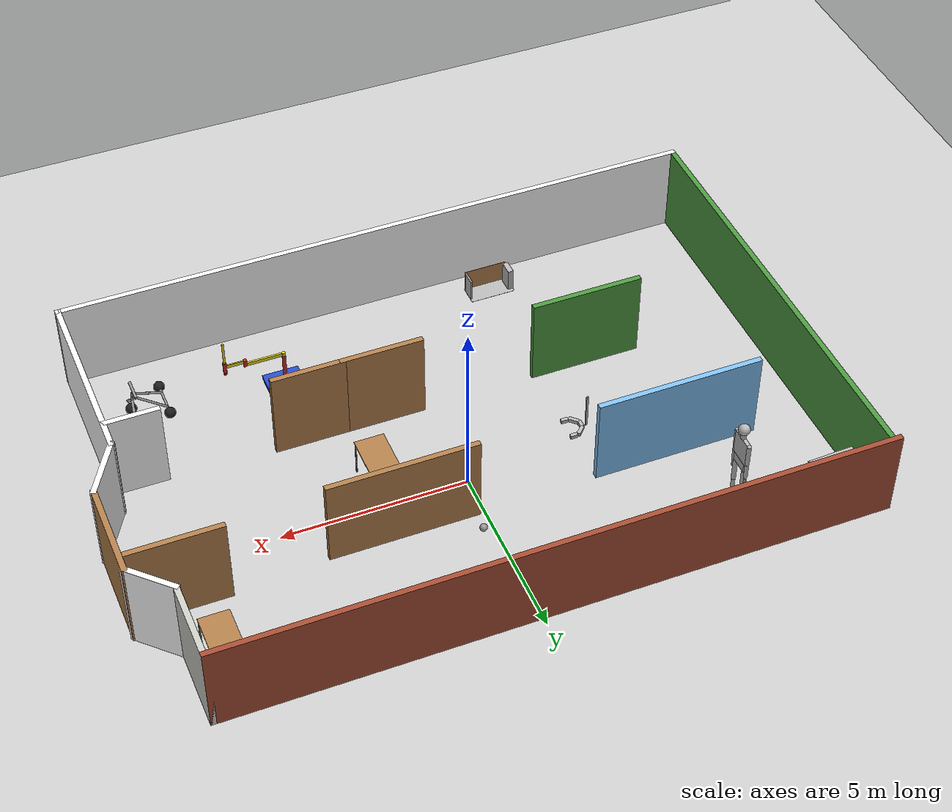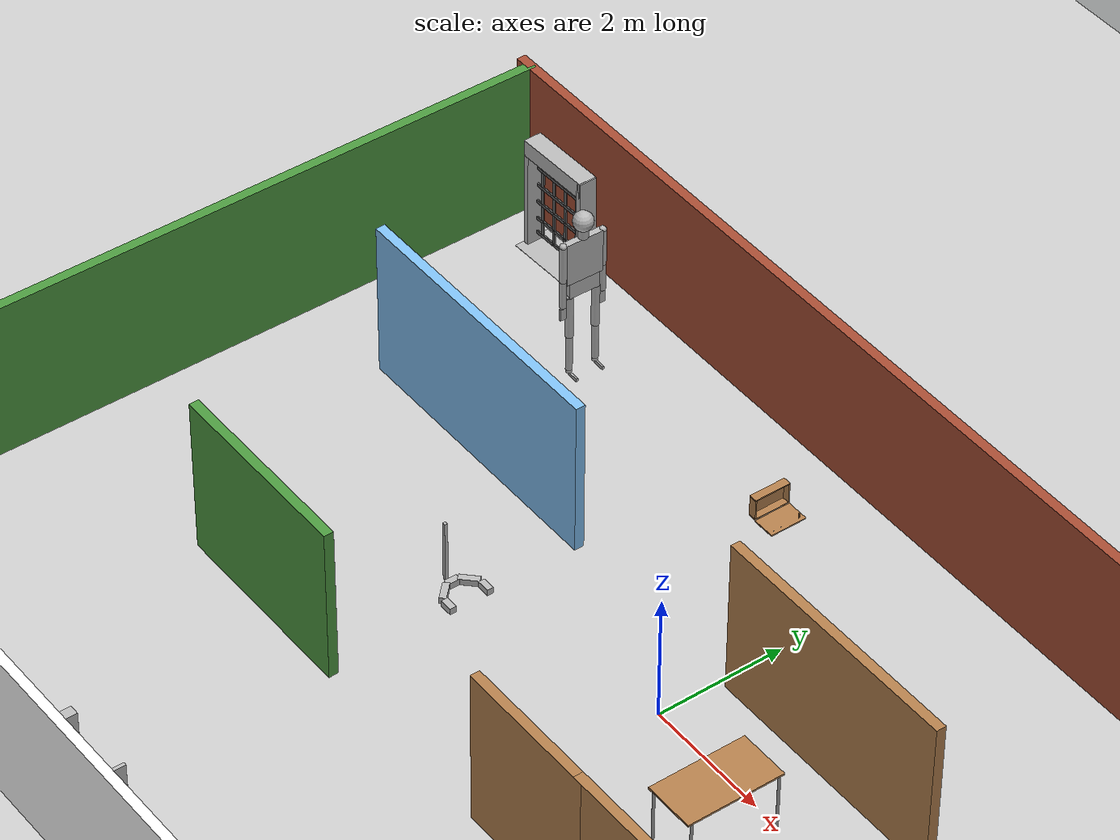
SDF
<sdf version="1.6">
 <world name="default">
  <light name="sun" type="directional">
   <pose>0 0 10 0 -0 0</pose>
   <diffuse>0.8 0.8 0.8 1</diffuse>
   <specular>0.2 0.2 0.2 1</specular>
   <attenuation>
    <range>1000</range>
    <constant>0.9</constant>
    <linear>0.01</linear>
    <quadratic>0.001</quadratic>
   </attenuation>
   <direction>-0.5 0.1 -0.9</direction>
  </light>
  <model name="ground_plane">
   <static>1</static>
   <link name="link">
    <collision name="collision">
     <geometry><plane><normal>0 0 1</normal><size>100 100</size></plane></geometry>
     <surface>
      <contact><collide_bitmask>65535</collide_bitmask></contact>
      <friction><ode><mu>100</mu><mu2>50</mu2></ode></friction>
     </surface>
    </collision>
    <visual name="visual">
     <cast_shadows>0</cast_shadows>
     <geometry><plane><normal>0 0 1</normal><size>100 100</size></plane></geometry>
     <material>
      <script><uri>file://media/materials/scripts/gazebo.material</uri><name>Gazebo/Grey</name></script>
     </material>
    </visual>
   </link>
  </model>
  <gravity>0 0 -9.8</gravity>
  <magnetic_field>6e-06 2.3e-05 -4.2e-05</magnetic_field>
  <atmosphere type="adiabatic"/>
  <physics name="default_physics" default="0" type="ode">
   <max_step_size>0.001</max_step_size>
   <real_time_factor>1</real_time_factor>
   <real_time_update_rate>1000</real_time_update_rate>
  </physics>
  <scene><ambient>0.4 0.4 0.4 1</ambient><background>0.7 0.7 0.7 1</background><shadows>1</shadows></scene>
  <spherical_coordinates>
   <surface_model>EARTH_WGS84</surface_model>
   <latitude_deg>0</latitude_deg>
   <longitude_deg>0</longitude_deg>
   <elevation>0</elevation>
   <heading_deg>0</heading_deg>
  </spherical_coordinates>
  <model name="mybuilding">
   <pose>-0.077377 -1.31008 0 0 -0 0</pose>
   <link name="Wall_10">
    <collision name="Wall_10_Collision">
     <geometry><box><size>17.75 0.15 2.5</size></box></geometry>
     <pose>0 0 1.25 0 -0 0</pose>
    </collision>
    <visual name="Wall_10_Visual">
     <pose>0 0 1.25 0 -0 0</pose>
     <geometry><box><size>17.75 0.15 2.5</size></box></geometry>
     <material>
      <script><uri>file://media/materials/scripts/gazebo.material</uri><name>Gazebo/Bricks</name></script>
      <ambient>1 1 1 1</ambient>
     </material>
     <meta><layer>0</layer></meta>
    </visual>
    <pose>-0.49283 6.05016 0 0 -0 0</pose>
   </link>
   <link name="Wall_11">
    <collision name="Wall_11_Collision">
     <geometry><box><size>2.25 0.15 2.5</size></box></geometry>
     <pose>0 0 1.25 0 -0 0</pose>
    </collision>
    <visual name="Wall_11_Visual">
     <pose>0 0 1.25 0 -0 0</pose>
     <geometry><box><size>2.25 0.15 2.5</size></box></geometry>
     <material>
      <script><uri>file://media/materials/scripts/gazebo.material</uri><name>Gazebo/CeilingTiled</name></script>
      <ambient>1 1 1 1</ambient>
     </material>
     <meta><layer>0</layer></meta>
    </visual>
    <pose>8.30717 5.00016 0 0 0 -1.5708</pose>
   </link>
   <link name="Wall_12">
    <collision name="Wall_12_Collision">
     <geometry><box><size>1.5 0.15 2.5</size></box></geometry>
     <pose>0 0 1.25 0 -0 0</pose>
    </collision>
    <visual name="Wall_12_Visual">
     <pose>0 0 1.25 0 -0 0</pose>
     <geometry><box><size>1.5 0.15 2.5</size></box></geometry>
     <material>
      <script><uri>file://media/materials/scripts/gazebo.material</uri><name>Gazebo/Secondary</name></script>
      <ambient>1 1 1 1</ambient>
     </material>
     <meta><layer>0</layer></meta>
    </visual>
    <pose>8.78447 3.47287 0 0 0 -0.785398</pose>
   </link>
   <link name="Wall_13">
    <collision name="Wall_13_Collision">
     <geometry><box><size>2.75 0.15 2.5</size></box></geometry>
     <pose>0 0 1.25 0 -0 0</pose>
    </collision>
    <visual name="Wall_13_Visual">
     <pose>0 0 1.25 0 -0 0</pose>
     <geometry><box><size>2.75 0.15 2.5</size></box></geometry>
     <material>
      <script><uri>file://media/materials/scripts/gazebo.material</uri><name>Gazebo/WoodPallet</name></script>
      <ambient>1 1 1 1</ambient>
     </material>
     <meta><layer>0</layer></meta>
    </visual>
    <pose>9.26177 1.69557 0 0 0 -1.5708</pose>
   </link>
   <link name="Wall_14">
    <collision name="Wall_14_Collision">
     <geometry><box><size>1.75 0.15 2.5</size></box></geometry>
     <pose>0 0 1.25 0 -0 0</pose>
    </collision>
    <visual name="Wall_14_Visual">
     <pose>0 0 1.25 0 -0 0</pose>
     <geometry><box><size>1.75 0.15 2.5</size></box></geometry>
     <material>
      <script><uri>file://media/materials/scripts/gazebo.material</uri><name>Gazebo/Primary</name></script>
      <ambient>1 1 1 1</ambient>
     </material>
     <meta><layer>0</layer></meta>
    </visual>
    <pose>8.86176 -0.297251 0 0 0 -2.0944</pose>
   </link>
   <link name="Wall_15">
    <collision name="Wall_15_Collision">
     <geometry><box><size>5.25 0.15 2.5</size></box></geometry>
     <pose>0 0 1.25 0 -0 0</pose>
    </collision>
    <visual name="Wall_15_Visual">
     <pose>0 0 1.25 0 -0 0</pose>
     <geometry><box><size>5.25 0.15 2.5</size></box></geometry>
     <material>
      <script><uri>file://media/materials/scripts/gazebo.material</uri><name>Gazebo/Tertiary</name></script>
      <ambient>1 1 1 1</ambient>
     </material>
     <meta><layer>0</layer></meta>
    </visual>
    <pose>8.46176 -3.54007 0 0 0 -1.5708</pose>
   </link>
   <link name="Wall_16">
    <collision name="Wall_16_Collision">
     <geometry><box><size>17.75 0.15 2.5</size></box></geometry>
     <pose>0 0 1.25 0 -0 0</pose>
    </collision>
    <visual name="Wall_16_Visual">
     <pose>0 0 1.25 0 -0 0</pose>
     <geometry><box><size>17.75 0.15 2.5</size></box></geometry>
     <material>
      <script><uri>file://media/materials/scripts/gazebo.material</uri><name>Gazebo/CoM</name></script>
      <ambient>1 1 1 1</ambient>
     </material>
     <meta><layer>0</layer></meta>
    </visual>
    <pose>-0.338236 -6.09007 0 0 -0 3.14159</pose>
   </link>
   <link name="Wall_17">
    <collision name="Wall_17_Collision">
     <geometry><box><size>12.25 0.15 2.5</size></box></geometry>
     <pose>0 0 1.25 0 -0 0</pose>
    </collision>
    <visual name="Wall_17_Visual">
     <pose>0 0 1.25 0 -0 0</pose>
     <geometry><box><size>12.25 0.15 2.5</size></box></geometry>
     <material>
      <script><uri>file://media/materials/scripts/gazebo.material</uri><name>Gazebo/Grass</name></script>
      <ambient>1 1 1 1</ambient>
     </material>
     <meta><layer>0</layer></meta>
    </visual>
    <pose>-9.13824 -0.040072 0 0 -0 1.5708</pose>
   </link>
   <link name="Wall_27">
    <collision name="Wall_27_Collision">
     <geometry><box><size>3.067 0.15 2.5</size></box></geometry>
     <pose>0 0 1.25 0 -0 0</pose>
    </collision>
    <visual name="Wall_27_Visual">
     <pose>0 0 1.25 0 -0 0</pose>
     <geometry><box><size>3.067 0.15 2.5</size></box></geometry>
     <material>
      <script><uri>file://media/materials/scripts/gazebo.material</uri><name>Gazebo/Grass</name></script>
      <ambient>1 1 1 1</ambient>
     </material>
     <meta><layer>0</layer></meta>
    </visual>
    <pose>-4.48112 -1.63592 0 0 -0 3.14159</pose>
   </link>
   <link name="Wall_45">
    <collision name="Wall_45_Collision">
     <geometry><box><size>2.25 0.15 2.5</size></box></geometry>
     <pose>0 0 1.25 0 -0 0</pose>
    </collision>
    <visual name="Wall_45_Visual">
     <pose>0 0 1.25 0 -0 0</pose>
     <geometry><box><size>2.25 0.15 2.5</size></box></geometry>
     <material>
      <script><uri>file://media/materials/scripts/gazebo.material</uri><name>Gazebo/WoodPallet</name></script>
      <ambient>1 1 1 1</ambient>
     </material>
     <meta><layer>0</layer></meta>
    </visual>
    <pose>1.24538 -1.59592 0 0 -0 3.14159</pose>
   </link>
   <link name="Wall_47">
    <collision name="Wall_47_Collision">
     <geometry><box><size>2 0.15 2.5</size></box></geometry>
     <pose>0 0 1.25 0 -0 0</pose>
    </collision>
    <visual name="Wall_47_Visual">
     <pose>0 0 1.25 0 -0 0</pose>
     <geometry><box><size>2 0.15 2.5</size></box></geometry>
     <material>
      <script><uri>file://media/materials/scripts/gazebo.material</uri><name>Gazebo/WoodFloor</name></script>
      <ambient>1 1 1 1</ambient>
     </material>
     <meta><layer>0</layer></meta>
    </visual>
    <pose>3.22038 -1.59592 0 0 -0 0</pose>
   </link>
   <link name="Wall_49">
    <collision name="Wall_49_Collision">
     <geometry><box><size>1.5 0.15 2.5</size></box></geometry>
     <pose>0 0 1.25 0 -0 0</pose>
    </collision>
    <visual name="Wall_49_Visual">
     <pose>0 0 1.25 0 -0 0</pose>
     <geometry><box><size>1.5 0.15 2.5</size></box></geometry>
     <material>
      <script><uri>file://media/materials/scripts/gazebo.material</uri><name>Gazebo/Footway</name></script>
      <ambient>1 1 1 1</ambient>
     </material>
     <meta><layer>0</layer></meta>
    </visual>
    <pose>7.76668 -1.71731 0 0 -0 0</pose>
   </link>
   <link name="Wall_53">
    <collision name="Wall_53_Collision">
     <geometry><box><size>2.5 0.15 2.5</size></box></geometry>
     <pose>0 0 1.25 0 -0 0</pose>
    </collision>
    <visual name="Wall_53_Visual">
     <pose>0 0 1.25 0 -0 0</pose>
     <geometry><box><size>2.5 0.15 2.5</size></box></geometry>
     <material>
      <script><uri>file://media/materials/scripts/gazebo.material</uri><name>Gazebo/Wood</name></script>
      <ambient>1 1 1 1</ambient>
     </material>
     <meta><layer>0</layer></meta>
    </visual>
    <pose>7.94303 2.57098 0 0 -0 0</pose>
   </link>
   <link name="Wall_55">
    <collision name="Wall_55_Collision">
     <geometry><box><size>4 0.15 2.5</size></box></geometry>
     <pose>0 0 1.25 0 -0 0</pose>
    </collision>
    <visual name="Wall_55_Visual">
     <pose>0 0 1.25 0 -0 0</pose>
     <geometry><box><size>4 0.15 2.5</size></box></geometry>
     <material>
      <script><uri>file://media/materials/scripts/gazebo.material</uri><name>Gazebo/Wood</name></script>
      <ambient>1 1 1 1</ambient>
     </material>
     <meta><layer>0</layer></meta>
    </visual>
    <pose>2.1875 2.3687 0 0 -0 3.14159</pose>
   </link>
   <link name="Wall_66">
    <collision name="Wall_66_Collision">
     <geometry><box><size>4.5 0.15 2.5</size></box></geometry>
     <pose>0 0 1.25 0 -0 0</pose>
    </collision>
    <visual name="Wall_66_Visual">
     <pose>0 0 1.25 0 -0 0</pose>
     <geometry><box><size>4.5 0.15 2.5</size></box></geometry>
     <material>
      <script><uri>file://media/materials/scripts/gazebo.material</uri><name>Gazebo/SkyBlue</name></script>
      <ambient>1 1 1 1</ambient>
     </material>
     <meta><layer>0</layer></meta>
    </visual>
    <pose>-5.23767 2.32825 0 0 -0 3.14159</pose>
   </link>
   <static>1</static>
  </model>
  <model name="table_clone_2">
   <static>1</static>
   <link name="link">
    <collision name="surface">
     <pose>0 0 1 0 -0 0</pose>
     <geometry><box><size>1.5 0.8 0.03</size></box></geometry>
     <surface><friction><ode><mu>0.6</mu><mu2>0.6</mu2></ode></friction></surface>
    </collision>
    <visual name="visual1">
     <pose>0 0 1 0 -0 0</pose>
     <geometry><box><size>1.5 0.8 0.03</size></box></geometry>
     <material>
      <script><uri>file://media/materials/scripts/gazebo.material</uri><name>Gazebo/Wood</name></script>
     </material>
    </visual>
    <collision name="front_left_leg">
     <pose>0.68 0.38 0.5 0 -0 0</pose>
     <geometry><cylinder><radius>0.02</radius><length>1</length></cylinder></geometry>
    </collision>
    <visual name="front_left_leg">
     <pose>0.68 0.38 0.5 0 -0 0</pose>
     <geometry><cylinder><radius>0.02</radius><length>1</length></cylinder></geometry>
     <material>
      <script><uri>file://media/materials/scripts/gazebo.material</uri><name>Gazebo/Grey</name></script>
     </material>
    </visual>
    <collision name="front_right_leg">
     <pose>0.68 -0.38 0.5 0 -0 0</pose>
     <geometry><cylinder><radius>0.02</radius><length>1</length></cylinder></geometry>
    </collision>
    <visual name="front_right_leg">
     <pose>0.68 -0.38 0.5 0 -0 0</pose>
     <geometry><cylinder><radius>0.02</radius><length>1</length></cylinder></geometry>
     <material>
      <script><uri>file://media/materials/scripts/gazebo.material</uri><name>Gazebo/Grey</name></script>
     </material>
    </visual>
    <collision name="back_right_leg">
     <pose>-0.68 -0.38 0.5 0 -0 0</pose>
     <geometry><cylinder><radius>0.02</radius><length>1</length></cylinder></geometry>
    </collision>
    <visual name="back_right_leg">
     <pose>-0.68 -0.38 0.5 0 -0 0</pose>
     <geometry><cylinder><radius>0.02</radius><length>1</length></cylinder></geometry>
     <material>
      <script><uri>file://media/materials/scripts/gazebo.material</uri><name>Gazebo/Grey</name></script>
     </material>
    </visual>
    <collision name="back_left_leg">
     <pose>-0.68 0.38 0.5 0 -0 0</pose>
     <geometry><cylinder><radius>0.02</radius><length>1</length></cylinder></geometry>
    </collision>
    <visual name="back_left_leg">
     <pose>-0.68 0.38 0.5 0 -0 0</pose>
     <geometry><cylinder><radius>0.02</radius><length>1</length></cylinder></geometry>
     <material>
      <script><uri>file://media/materials/scripts/gazebo.material</uri><name>Gazebo/Grey</name></script>
     </material>
    </visual>
   </link>
   <pose>2.09551 -0.734988 0 0 0 -1.57312</pose>
  </model>
  <model name="table_clone_4">
   <static>1</static>
   <link name="link">
    <collision name="surface">
     <pose>0 0 1 0 -0 0</pose>
     <geometry><box><size>1.5 0.8 0.03</size></box></geometry>
     <surface><friction><ode><mu>0.6</mu><mu2>0.6</mu2></ode></friction></surface>
    </collision>
    <visual name="visual1">
     <pose>0 0 1 0 -0 0</pose>
     <geometry><box><size>1.5 0.8 0.03</size></box></geometry>
     <material>
      <script><uri>file://media/materials/scripts/gazebo.material</uri><name>Gazebo/Wood</name></script>
     </material>
    </visual>
    <collision name="front_left_leg">
     <pose>0.68 0.38 0.5 0 -0 0</pose>
     <geometry><cylinder><radius>0.02</radius><length>1</length></cylinder></geometry>
    </collision>
    <visual name="front_left_leg">
     <pose>0.68 0.38 0.5 0 -0 0</pose>
     <geometry><cylinder><radius>0.02</radius><length>1</length></cylinder></geometry>
     <material>
      <script><uri>file://media/materials/scripts/gazebo.material</uri><name>Gazebo/Grey</name></script>
     </material>
    </visual>
    <collision name="front_right_leg">
     <pose>0.68 -0.38 0.5 0 -0 0</pose>
     <geometry><cylinder><radius>0.02</radius><length>1</length></cylinder></geometry>
    </collision>
    <visual name="front_right_leg">
     <pose>0.68 -0.38 0.5 0 -0 0</pose>
     <geometry><cylinder><radius>0.02</radius><length>1</length></cylinder></geometry>
     <material>
      <script><uri>file://media/materials/scripts/gazebo.material</uri><name>Gazebo/Grey</name></script>
     </material>
    </visual>
    <collision name="back_right_leg">
     <pose>-0.68 -0.38 0.5 0 -0 0</pose>
     <geometry><cylinder><radius>0.02</radius><length>1</length></cylinder></geometry>
    </collision>
    <visual name="back_right_leg">
     <pose>-0.68 -0.38 0.5 0 -0 0</pose>
     <geometry><cylinder><radius>0.02</radius><length>1</length></cylinder></geometry>
     <material>
      <script><uri>file://media/materials/scripts/gazebo.material</uri><name>Gazebo/Grey</name></script>
     </material>
    </visual>
    <collision name="back_left_leg">
     <pose>-0.68 0.38 0.5 0 -0 0</pose>
     <geometry><cylinder><radius>0.02</radius><length>1</length></cylinder></geometry>
    </collision>
    <visual name="back_left_leg">
     <pose>-0.68 0.38 0.5 0 -0 0</pose>
     <geometry><cylinder><radius>0.02</radius><length>1</length></cylinder></geometry>
     <material>
      <script><uri>file://media/materials/scripts/gazebo.material</uri><name>Gazebo/Grey</name></script>
     </material>
    </visual>
   </link>
   <pose>7.4382 3.26988 0 0 0 -1.57312</pose>
  </model>
  <audio><device>default</device></audio>
  <model name="my_sphere">
   <link name="link">
    <inertial>
     <mass>1</mass>
     <inertia><ixx>0.1</ixx><ixy>0</ixy><ixz>0</ixz><iyy>0.1</iyy><iyz>0</iyz><izz>0.1</izz></inertia>
    </inertial>
    <visual name="visual">
     <geometry><sphere><radius>0.1</radius></sphere></geometry>
     <material>
      <script><name>Gazebo/Grey</name><uri>file://media/materials/scripts/gazebo.material</uri></script>
      <shader type="pixel"><normal_map>__default__</normal_map></shader>
      <ambient>1 1 1 1</ambient>
      <diffuse>1 1 1 1</diffuse>
      <specular>1 1 1 1</specular>
      <emissive>1 1 1 1</emissive>
     </material>
    </visual>
    <collision name="collision">
     <geometry><sphere><radius>0.1</radius></sphere></geometry>
     <surface>
      <friction>
       <ode><mu>1</mu><mu2>1</mu2><fdir1>0 0 0</fdir1><slip1>0</slip1><slip2>0</slip2></ode>
       <torsional>
        <coefficient>1</coefficient>
        <patch_radius>0</patch_radius>
        <surface_radius>0</surface_radius>
        <use_patch_radius>1</use_patch_radius>
        <ode><slip>0</slip></ode>
       </torsional>
      </friction>
      <bounce><restitution_coefficient>0</restitution_coefficient><threshold>1e+06</threshold></bounce>
      <contact>
       <collide_without_contact>0</collide_without_contact>
       <collide_without_contact_bitmask>1</collide_without_contact_bitmask>
       <collide_bitmask>1</collide_bitmask>
       <ode>
        <soft_cfm>0</soft_cfm>
        <soft_erp>0.2</soft_erp>
        <kp>1e+13</kp>
        <kd>1</kd>
        <max_vel>0.01</max_vel>
        <min_depth>0</min_depth>
       </ode>
       <bullet>
        <split_impulse>1</split_impulse>
        <split_impulse_penetration_threshold>-0.01</split_impulse_penetration_threshold>
        <soft_cfm>0</soft_cfm>
        <soft_erp>0.2</soft_erp>
        <kp>1e+13</kp>
        <kd>1</kd>
       </bullet>
      </contact>
     </surface>
    </collision>
   </link>
   <static>0</static>
   <pose>0.251743 1.65501 0.1 0 -0 0</pose>
  </model>
  <model name="simple_arm">
   <link name="arm_base">
    <inertial>
     <pose>0 0 0.00099 0 -0 0</pose>
     <inertia><ixx>1.11</ixx><ixy>0</ixy><ixz>0</ixz><iyy>100.11</iyy><iyz>0</iyz><izz>1.01</izz></inertia>
     <mass>101</mass>
    </inertial>
    <collision name="arm_base_geom">
     <pose>0 0 0.05 0 -0 0</pose>
     <geometry><box><size>1 1 0.1</size></box></geometry>
    </collision>
    <visual name="arm_base_geom_visual">
     <pose>0 0 0.05 0 -0 0</pose>
     <geometry><box><size>1 1 0.1</size></box></geometry>
     <material>
      <script><uri>file://media/materials/scripts/gazebo.material</uri><name>Gazebo/Blue</name></script>
     </material>
    </visual>
    <collision name="arm_base_geom_arm_trunk">
     <pose>0 0 0.6 0 -0 0</pose>
     <geometry><cylinder><radius>0.05</radius><length>1</length></cylinder></geometry>
    </collision>
    <visual name="arm_base_geom_arm_trunk_visual">
     <pose>0 0 0.6 0 -0 0</pose>
     <geometry><cylinder><radius>0.05</radius><length>1</length></cylinder></geometry>
     <material>
      <script><uri>file://media/materials/scripts/gazebo.material</uri><name>Gazebo/Red</name></script>
     </material>
    </visual>
   </link>
   <link name="arm_shoulder_pan">
    <pose>0 0 1.1 0 -0 0</pose>
    <inertial>
     <pose>0.045455 0 0 0 -0 0</pose>
     <inertia><ixx>0.011</ixx><ixy>0</ixy><ixz>0</ixz><iyy>0.0225</iyy><iyz>0</iyz><izz>0.0135</izz></inertia>
     <mass>1.1</mass>
    </inertial>
    <collision name="arm_shoulder_pan_geom">
     <pose>0 0 0.05 0 -0 0</pose>
     <geometry><cylinder><radius>0.05</radius><length>0.1</length></cylinder></geometry>
    </collision>
    <visual name="arm_shoulder_pan_geom_visual">
     <pose>0 0 0.05 0 -0 0</pose>
     <geometry><cylinder><radius>0.05</radius><length>0.1</length></cylinder></geometry>
     <material>
      <script><uri>file://media/materials/scripts/gazebo.material</uri><name>Gazebo/Yellow</name></script>
     </material>
    </visual>
    <collision name="arm_shoulder_pan_geom_arm_shoulder">
     <pose>0.55 0 0.05 0 -0 0</pose>
     <geometry><box><size>1 0.05 0.1</size></box></geometry>
    </collision>
    <visual name="arm_shoulder_pan_geom_arm_shoulder_visual">
     <pose>0.55 0 0.05 0 -0 0</pose>
     <geometry><box><size>1 0.05 0.1</size></box></geometry>
     <material>
      <script><uri>file://media/materials/scripts/gazebo.material</uri><name>Gazebo/Yellow</name></script>
     </material>
    </visual>
   </link>
   <link name="arm_elbow_pan">
    <pose>1.05 0 1.1 0 -0 0</pose>
    <inertial>
     <pose>0.0875 0 0.083333 0 -0 0</pose>
     <inertia>
      <ixx>0.031</ixx>
      <ixy>0</ixy>
      <ixz>0.005</ixz>
      <iyy>0.07275</iyy>
      <iyz>0</iyz>
      <izz>0.04475</izz>
     </inertia>
     <mass>1.2</mass>
    </inertial>
    <collision name="arm_elbow_pan_geom">
     <pose>0 0 0.1 0 -0 0</pose>
     <geometry><cylinder><radius>0.05</radius><length>0.2</length></cylinder></geometry>
    </collision>
    <visual name="arm_elbow_pan_geom_visual">
     <pose>0 0 0.1 0 -0 0</pose>
     <geometry><cylinder><radius>0.05</radius><length>0.2</length></cylinder></geometry>
     <material>
      <script><uri>file://media/materials/scripts/gazebo.material</uri><name>Gazebo/Red</name></script>
     </material>
    </visual>
    <collision name="arm_elbow_pan_geom_arm_elbow">
     <pose>0.3 0 0.15 0 -0 0</pose>
     <geometry><box><size>0.5 0.03 0.1</size></box></geometry>
    </collision>
    <visual name="arm_elbow_pan_geom_arm_elbow_visual">
     <pose>0.3 0 0.15 0 -0 0</pose>
     <geometry><box><size>0.5 0.03 0.1</size></box></geometry>
     <material>
      <script><uri>file://media/materials/scripts/gazebo.material</uri><name>Gazebo/Yellow</name></script>
     </material>
    </visual>
    <collision name="arm_elbow_pan_geom_arm_wrist">
     <pose>0.55 0 0.15 0 -0 0</pose>
     <geometry><cylinder><radius>0.05</radius><length>0.3</length></cylinder></geometry>
    </collision>
    <visual name="arm_elbow_pan_geom_arm_wrist_visual">
     <pose>0.55 0 0.15 0 -0 0</pose>
     <geometry><cylinder><radius>0.05</radius><length>0.3</length></cylinder></geometry>
     <material>
      <script><uri>file://media/materials/scripts/gazebo.material</uri><name>Gazebo/Red</name></script>
     </material>
    </visual>
   </link>
   <link name="arm_wrist_lift">
    <pose>1.6 0 1.05 0 -0 0</pose>
    <inertial>
     <inertia><ixx>0.01</ixx><ixy>0</ixy><ixz>0</ixz><iyy>0.01</iyy><iyz>0</iyz><izz>0.001</izz></inertia>
     <mass>0.1</mass>
    </inertial>
    <collision name="arm_wrist_lift_geom">
     <pose>0 0 0.5 0 -0 0</pose>
     <geometry><cylinder><radius>0.03</radius><length>1</length></cylinder></geometry>
    </collision>
    <visual name="arm_wrist_lift_geom_visual">
     <pose>0 0 0.5 0 -0 0</pose>
     <geometry><cylinder><radius>0.03</radius><length>1</length></cylinder></geometry>
     <material>
      <script><uri>file://media/materials/scripts/gazebo.material</uri><name>Gazebo/Yellow</name></script>
     </material>
    </visual>
   </link>
   <link name="arm_wrist_roll">
    <pose>1.6 0 1 0 -0 0</pose>
    <inertial>
     <inertia><ixx>0.01</ixx><ixy>0</ixy><ixz>0</ixz><iyy>0.01</iyy><iyz>0</iyz><izz>0.001</izz></inertia>
     <mass>0.1</mass>
    </inertial>
    <collision name="arm_wrist_roll_geom">
     <pose>0 0 0.025 0 -0 0</pose>
     <geometry><cylinder><radius>0.05</radius><length>0.05</length></cylinder></geometry>
    </collision>
    <visual name="arm_wrist_roll_geom_visual">
     <pose>0 0 0.025 0 -0 0</pose>
     <geometry><cylinder><radius>0.05</radius><length>0.05</length></cylinder></geometry>
     <material>
      <script><uri>file://media/materials/scripts/gazebo.material</uri><name>Gazebo/Red</name></script>
     </material>
    </visual>
   </link>
   <joint name="arm_shoulder_pan_joint" type="revolute">
    <parent>arm_base</parent>
    <child>arm_shoulder_pan</child>
    <axis>
     <dynamics>
      <damping>1</damping>
      <friction>0</friction>
      <spring_reference>0</spring_reference>
      <spring_stiffness>0</spring_stiffness>
     </dynamics>
     <xyz>0 0 1</xyz>
     <use_parent_model_frame>1</use_parent_model_frame>
     <limit><lower>-1e+16</lower><upper>1e+16</upper></limit>
    </axis>
   </joint>
   <joint name="arm_elbow_pan_joint" type="revolute">
    <parent>arm_shoulder_pan</parent>
    <child>arm_elbow_pan</child>
    <axis>
     <dynamics>
      <damping>1</damping>
      <friction>0</friction>
      <spring_reference>0</spring_reference>
      <spring_stiffness>0</spring_stiffness>
     </dynamics>
     <xyz>0 0 1</xyz>
     <use_parent_model_frame>1</use_parent_model_frame>
     <limit><lower>-1e+16</lower><upper>1e+16</upper></limit>
    </axis>
   </joint>
   <joint name="arm_wrist_lift_joint" type="prismatic">
    <parent>arm_elbow_pan</parent>
    <child>arm_wrist_lift</child>
    <axis>
     <dynamics>
      <damping>1</damping>
      <friction>0</friction>
      <spring_reference>0</spring_reference>
      <spring_stiffness>0</spring_stiffness>
     </dynamics>
     <limit><lower>-0.8</lower><upper>0.1</upper></limit>
     <xyz>0 0 1</xyz>
     <use_parent_model_frame>1</use_parent_model_frame>
    </axis>
   </joint>
   <joint name="arm_wrist_roll_joint" type="revolute">
    <parent>arm_wrist_lift</parent>
    <child>arm_wrist_roll</child>
    <axis>
     <dynamics>
      <damping>1</damping>
      <friction>0</friction>
      <spring_reference>0</spring_reference>
      <spring_stiffness>0</spring_stiffness>
     </dynamics>
     <limit><lower>-2.99999</lower><upper>2.99999</upper></limit>
     <xyz>0 0 1</xyz>
     <use_parent_model_frame>1</use_parent_model_frame>
    </axis>
   </joint>
   <pose>3.12467 -5.08041 0 0 0 -0.000925</pose>
  </model>
  <model name="simple_gripper">
   <link name="riser">
    <pose>-0.15 0 0.5 0 -0 0</pose>
    <inertial>
     <mass>10</mass>
     <inertia><ixx>1</ixx><ixy>0</ixy><ixz>0</ixz><iyy>1</iyy><iyz>0</iyz><izz>1</izz></inertia>
    </inertial>
    <collision name="collision">
     <geometry><box><size>0.05 0.05 1</size></box></geometry>
     <surface><contact><ode><max_vel>0</max_vel></ode></contact></surface>
    </collision>
    <visual name="visual"><geometry><box><size>0.05 0.05 1</size></box></geometry></visual>
   </link>
   <link name="palm">
    <pose>0 0 0.05 0 -0 0</pose>
    <inertial>
     <mass>0.5</mass>
     <inertia><ixx>1</ixx><ixy>0</ixy><ixz>0</ixz><iyy>1</iyy><iyz>0</iyz><izz>1</izz></inertia>
    </inertial>
    <collision name="collision">
     <geometry><box><size>0.1 0.2 0.1</size></box></geometry>
     <surface><contact><ode><max_vel>0</max_vel></ode></contact></surface>
    </collision>
    <visual name="visual"><geometry><box><size>0.1 0.2 0.1</size></box></geometry></visual>
   </link>
   <link name="left_finger">
    <pose>0.1 0.2 0.05 0 0 -0.78539</pose>
    <inertial>
     <mass>0.1</mass>
     <inertia><ixx>1</ixx><ixy>0</ixy><ixz>0</ixz><iyy>1</iyy><iyz>0</iyz><izz>1</izz></inertia>
    </inertial>
    <collision name="collision">
     <geometry><box><size>0.1 0.3 0.1</size></box></geometry>
     <surface>
      <friction><ode><mu>0.1</mu><mu2>0</mu2></ode></friction>
      <contact><ode><max_vel>0</max_vel></ode></contact>
     </surface>
    </collision>
    <visual name="visual"><geometry><box><size>0.1 0.3 0.1</size></box></geometry></visual>
   </link>
   <link name="left_finger_tip">
    <pose>0.336 0.3 0.05 0 -0 1.5707</pose>
    <inertial>
     <mass>0.5</mass>
     <inertia><ixx>1</ixx><ixy>0</ixy><ixz>0</ixz><iyy>1</iyy><iyz>0</iyz><izz>1</izz></inertia>
    </inertial>
    <collision name="collision">
     <geometry><box><size>0.1 0.2 0.1</size></box></geometry>
     <surface>
      <friction><ode><mu>0.1</mu><mu2>0</mu2></ode></friction>
      <contact><ode><max_vel>0</max_vel></ode></contact>
     </surface>
    </collision>
    <visual name="visual"><geometry><box><size>0.1 0.2 0.1</size></box></geometry></visual>
   </link>
   <link name="right_finger">
    <pose>0.1 -0.2 0.05 0 -0 0.78539</pose>
    <inertial>
     <mass>0.1</mass>
     <inertia><ixx>1</ixx><ixy>0</ixy><ixz>0</ixz><iyy>1</iyy><iyz>0</iyz><izz>1</izz></inertia>
    </inertial>
    <collision name="collision">
     <geometry><box><size>0.1 0.3 0.1</size></box></geometry>
     <surface>
      <friction><ode><mu>0.1</mu><mu2>0</mu2></ode></friction>
      <contact><ode><max_vel>0</max_vel></ode></contact>
     </surface>
    </collision>
    <visual name="visual"><geometry><box><size>0.1 0.3 0.1</size></box></geometry></visual>
   </link>
   <link name="right_finger_tip">
    <pose>0.336 -0.3 0.05 0 -0 1.5707</pose>
    <inertial>
     <mass>0.1</mass>
     <inertia><ixx>1</ixx><ixy>0</ixy><ixz>0</ixz><iyy>1</iyy><iyz>0</iyz><izz>1</izz></inertia>
    </inertial>
    <collision name="collision">
     <geometry><box><size>0.1 0.2 0.1</size></box></geometry>
     <surface>
      <friction><ode><mu>0.1</mu><mu2>0</mu2></ode></friction>
      <contact><ode><max_vel>0</max_vel></ode></contact>
     </surface>
    </collision>
    <visual name="visual"><geometry><box><size>0.1 0.2 0.1</size></box></geometry></visual>
   </link>
   <joint name="palm_left_finger" type="revolute">
    <pose>0 -0.15 0 0 -0 0</pose>
    <child>left_finger</child>
    <parent>palm</parent>
    <axis>
     <limit><lower>-0.8</lower><upper>0.8</upper></limit>
     <xyz>0 0 1</xyz>
     <use_parent_model_frame>1</use_parent_model_frame>
     <dynamics><spring_reference>0</spring_reference><spring_stiffness>0</spring_stiffness></dynamics>
    </axis>
   </joint>
   <joint name="left_finger_tip" type="revolute">
    <pose>0 0.1 0 0 -0 0</pose>
    <child>left_finger_tip</child>
    <parent>left_finger</parent>
    <axis>
     <limit><lower>-0.8</lower><upper>0.8</upper></limit>
     <xyz>0 0 1</xyz>
     <use_parent_model_frame>1</use_parent_model_frame>
     <dynamics><spring_reference>0</spring_reference><spring_stiffness>0</spring_stiffness></dynamics>
    </axis>
   </joint>
   <joint name="palm_right_finger" type="revolute">
    <pose>0 0.15 0 0 -0 0</pose>
    <child>right_finger</child>
    <parent>palm</parent>
    <axis>
     <limit><lower>-0.8</lower><upper>0.8</upper></limit>
     <xyz>0 0 1</xyz>
     <use_parent_model_frame>1</use_parent_model_frame>
     <dynamics><spring_reference>0</spring_reference><spring_stiffness>0</spring_stiffness></dynamics>
    </axis>
   </joint>
   <joint name="right_finger_tip" type="revolute">
    <pose>0 0.1 0 0 -0 0</pose>
    <child>right_finger_tip</child>
    <parent>right_finger</parent>
    <axis>
     <limit><lower>-0.8</lower><upper>0.8</upper></limit>
     <xyz>0 0 1</xyz>
     <use_parent_model_frame>1</use_parent_model_frame>
     <dynamics><spring_reference>0</spring_reference><spring_stiffness>0</spring_stiffness></dynamics>
    </axis>
   </joint>
   <joint name="palm_riser" type="prismatic">
    <child>palm</child>
    <parent>riser</parent>
    <axis>
     <limit><lower>0</lower><upper>0.9</upper></limit>
     <xyz>0 0 1</xyz>
     <use_parent_model_frame>1</use_parent_model_frame>
     <dynamics><spring_reference>0</spring_reference><spring_stiffness>0</spring_stiffness></dynamics>
    </axis>
   </joint>
   <gripper name="simple_gripper">
    <grasp_check>
     <detach_steps>40</detach_steps>
     <attach_steps>20</attach_steps>
     <min_contact_count>2</min_contact_count>
    </grasp_check>
    <gripper_link>right_finger</gripper_link>
    <gripper_link>right_finger_tip</gripper_link>
    <gripper_link>left_finger</gripper_link>
    <gripper_link>left_finger_tip</gripper_link>
    <palm_link>palm</palm_link>
   </gripper>
   <pose>-3.48047 -0.744463 -1e-05 0 -0 0.003331</pose>
  </model>
  <model name="ragdoll">
   <pose>-5.92866 3.198 1.39999 -2e-06 -0.00097 -0.018251</pose>
   <link name="hip">
    <inertial>
     <inertia><ixx>0.1</ixx><ixy>0</ixy><ixz>0</ixz><iyy>0.1</iyy><iyz>0</iyz><izz>0.1</izz></inertia>
     <mass>10</mass>
    </inertial>
    <collision name="hip_geom">
     <pose>0 0 0.125 0 -0 0</pose>
     <geometry><box><size>0.1 0.5 0.25</size></box></geometry>
     <surface>
      <friction><ode><mu>-1</mu><mu2>-1</mu2><fdir1>0 0 0</fdir1><slip1>0</slip1><slip2>0</slip2></ode></friction>
      <bounce><restitution_coefficient>0</restitution_coefficient><threshold>100000</threshold></bounce>
      <contact>
       <ode>
        <soft_cfm>0</soft_cfm>
        <soft_erp>0.2</soft_erp>
        <kp>1e+12</kp>
        <kd>1</kd>
        <max_vel>0</max_vel>
        <min_depth>0.001</min_depth>
       </ode>
      </contact>
     </surface>
    </collision>
    <visual name="hip_geom_visual">
     <pose>0 0 0.125 0 -0 0</pose>
     <geometry><box><size>0.1 0.5 0.25</size></box></geometry>
    </visual>
    <gravity>0</gravity>
   </link>
   <link name="l_thigh_pan">
    <pose>0 0.22 0 0 -0 0</pose>
    <inertial>
     <inertia><ixx>0.01</ixx><ixy>0</ixy><ixz>0</ixz><iyy>0.01</iyy><iyz>0</iyz><izz>0.01</izz></inertia>
     <mass>1</mass>
    </inertial>
    <collision name="l_thigh_pan_geom">
     <pose>0 0 -0.03 0 -0 0</pose>
     <geometry><sphere><radius>0.06</radius></sphere></geometry>
     <surface>
      <friction><ode><mu>-1</mu><mu2>-1</mu2><fdir1>0 0 0</fdir1><slip1>0</slip1><slip2>0</slip2></ode></friction>
      <bounce><restitution_coefficient>0</restitution_coefficient><threshold>100000</threshold></bounce>
      <contact>
       <ode>
        <soft_cfm>0</soft_cfm>
        <soft_erp>0.2</soft_erp>
        <kp>1e+12</kp>
        <kd>1</kd>
        <max_vel>0</max_vel>
        <min_depth>0.001</min_depth>
       </ode>
      </contact>
     </surface>
    </collision>
    <visual name="l_thigh_pan_geom_visual">
     <pose>0 0 -0.03 0 -0 0</pose>
     <geometry><sphere><radius>0.06</radius></sphere></geometry>
    </visual>
    <gravity>0</gravity>
   </link>
   <link name="l_thigh_lift">
    <pose>0 0.22 0 0 -0 0</pose>
    <inertial>
     <inertia><ixx>0.05</ixx><ixy>0</ixy><ixz>0</ixz><iyy>0.05</iyy><iyz>0</iyz><izz>0.05</izz></inertia>
     <mass>5</mass>
    </inertial>
    <collision name="l_thigh_lift_geom">
     <pose>0 0 -0.35 0 -0 0</pose>
     <geometry><cylinder><radius>0.06</radius><length>0.7</length></cylinder></geometry>
     <surface>
      <friction><ode><mu>-1</mu><mu2>-1</mu2><fdir1>0 0 0</fdir1><slip1>0</slip1><slip2>0</slip2></ode></friction>
      <bounce><restitution_coefficient>0</restitution_coefficient><threshold>100000</threshold></bounce>
      <contact>
       <ode>
        <soft_cfm>0</soft_cfm>
        <soft_erp>0.2</soft_erp>
        <kp>1e+12</kp>
        <kd>1</kd>
        <max_vel>0</max_vel>
        <min_depth>0.001</min_depth>
       </ode>
      </contact>
     </surface>
    </collision>
    <visual name="l_thigh_lift_geom_visual">
     <pose>0 0 -0.35 0 -0 0</pose>
     <geometry><cylinder><radius>0.06</radius><length>0.7</length></cylinder></geometry>
    </visual>
    <gravity>0</gravity>
   </link>
   <link name="l_calf">
    <pose>0 0.22 -0.7 0 -0 0</pose>
    <inertial>
     <inertia><ixx>0.02</ixx><ixy>0</ixy><ixz>0</ixz><iyy>0.02</iyy><iyz>0</iyz><izz>0.02</izz></inertia>
     <mass>2</mass>
    </inertial>
    <collision name="l_calf_geom">
     <pose>0 0 -0.3 0 -0 0</pose>
     <geometry><cylinder><radius>0.05</radius><length>0.6</length></cylinder></geometry>
     <surface>
      <friction><ode><mu>-1</mu><mu2>-1</mu2><fdir1>0 0 0</fdir1><slip1>0</slip1><slip2>0</slip2></ode></friction>
      <bounce><restitution_coefficient>0</restitution_coefficient><threshold>100000</threshold></bounce>
      <contact>
       <ode>
        <soft_cfm>0</soft_cfm>
        <soft_erp>0.2</soft_erp>
        <kp>1e+12</kp>
        <kd>1</kd>
        <max_vel>0</max_vel>
        <min_depth>0.001</min_depth>
       </ode>
      </contact>
     </surface>
    </collision>
    <visual name="l_calf_geom_visual">
     <pose>0 0 -0.3 0 -0 0</pose>
     <geometry><cylinder><radius>0.05</radius><length>0.6</length></cylinder></geometry>
    </visual>
    <gravity>0</gravity>
   </link>
   <link name="l_ankle">
    <pose>0 0.22 -1.325 0 -0 0</pose>
    <inertial>
     <inertia><ixx>0.01</ixx><ixy>0</ixy><ixz>0</ixz><iyy>0.01</iyy><iyz>0</iyz><izz>0.01</izz></inertia>
     <mass>1</mass>
    </inertial>
    <collision name="l_ankle_geom">
     <geometry><sphere><radius>0.05</radius></sphere></geometry>
     <surface>
      <friction><ode><mu>-1</mu><mu2>-1</mu2><fdir1>0 0 0</fdir1><slip1>0</slip1><slip2>0</slip2></ode></friction>
      <bounce><restitution_coefficient>0</restitution_coefficient><threshold>100000</threshold></bounce>
      <contact>
       <ode>
        <soft_cfm>0</soft_cfm>
        <soft_erp>0.2</soft_erp>
        <kp>1e+12</kp>
        <kd>1</kd>
        <max_vel>0</max_vel>
        <min_depth>0.001</min_depth>
       </ode>
      </contact>
     </surface>
    </collision>
    <visual name="l_ankle_geom_visual"><geometry><sphere><radius>0.05</radius></sphere></geometry></visual>
    <gravity>0</gravity>
   </link>
   <link name="l_foot">
    <pose>0 0.22 -1.35 0 -0 0</pose>
    <inertial>
     <pose>0.1 0 0 0 -0 0</pose>
     <inertia><ixx>0.01</ixx><ixy>0</ixy><ixz>0</ixz><iyy>0.01</iyy><iyz>0</iyz><izz>0.01</izz></inertia>
     <mass>1</mass>
    </inertial>
    <collision name="l_foot_geom">
     <pose>0.1 0 -0.025 0 -0 0</pose>
     <geometry><box><size>0.2 0.03 0.05</size></box></geometry>
     <surface>
      <friction><ode><mu>-1</mu><mu2>-1</mu2><fdir1>0 0 0</fdir1><slip1>0</slip1><slip2>0</slip2></ode></friction>
      <bounce><restitution_coefficient>0</restitution_coefficient><threshold>100000</threshold></bounce>
      <contact>
       <ode>
        <soft_cfm>0</soft_cfm>
        <soft_erp>0.2</soft_erp>
        <kp>1e+12</kp>
        <kd>1</kd>
        <max_vel>0</max_vel>
        <min_depth>0.001</min_depth>
       </ode>
      </contact>
     </surface>
    </collision>
    <visual name="l_foot_geom_visual">
     <pose>0.1 0 -0.025 0 -0 0</pose>
     <geometry><box><size>0.2 0.03 0.05</size></box></geometry>
    </visual>
   </link>
   <link name="r_thigh_pan">
    <pose>0 -0.22 0 0 -0 0</pose>
    <inertial>
     <inertia><ixx>0.01</ixx><ixy>0</ixy><ixz>0</ixz><iyy>0.01</iyy><iyz>0</iyz><izz>0.01</izz></inertia>
     <mass>1</mass>
    </inertial>
    <collision name="r_thigh_pan_geom">
     <pose>0 0 -0.03 0 -0 0</pose>
     <geometry><sphere><radius>0.06</radius></sphere></geometry>
     <surface>
      <friction><ode><mu>-1</mu><mu2>-1</mu2><fdir1>0 0 0</fdir1><slip1>0</slip1><slip2>0</slip2></ode></friction>
      <bounce><restitution_coefficient>0</restitution_coefficient><threshold>100000</threshold></bounce>
      <contact>
       <ode>
        <soft_cfm>0</soft_cfm>
        <soft_erp>0.2</soft_erp>
        <kp>1e+12</kp>
        <kd>1</kd>
        <max_vel>0</max_vel>
        <min_depth>0.001</min_depth>
       </ode>
      </contact>
     </surface>
    </collision>
    <visual name="r_thigh_pan_geom_visual">
     <pose>0 0 -0.03 0 -0 0</pose>
     <geometry><sphere><radius>0.06</radius></sphere></geometry>
    </visual>
    <gravity>0</gravity>
   </link>
   <link name="r_thigh_lift">
    <pose>0 -0.22 0 0 -0 0</pose>
    <inertial>
     <inertia><ixx>0.05</ixx><ixy>0</ixy><ixz>0</ixz><iyy>0.05</iyy><iyz>0</iyz><izz>0.05</izz></inertia>
     <mass>5</mass>
    </inertial>
    <collision name="r_thigh_lift_geom">
     <pose>0 0 -0.35 0 -0 0</pose>
     <geometry><cylinder><radius>0.06</radius><length>0.7</length></cylinder></geometry>
     <surface>
      <friction><ode><mu>-1</mu><mu2>-1</mu2><fdir1>0 0 0</fdir1><slip1>0</slip1><slip2>0</slip2></ode></friction>
      <bounce><restitution_coefficient>0</restitution_coefficient><threshold>100000</threshold></bounce>
      <contact>
       <ode>
        <soft_cfm>0</soft_cfm>
        <soft_erp>0.2</soft_erp>
        <kp>1e+12</kp>
        <kd>1</kd>
        <max_vel>0</max_vel>
        <min_depth>0.001</min_depth>
       </ode>
      </contact>
     </surface>
    </collision>
    <visual name="r_thigh_lift_geom_visual">
     <pose>0 0 -0.35 0 -0 0</pose>
     <geometry><cylinder><radius>0.06</radius><length>0.7</length></cylinder></geometry>
    </visual>
    <gravity>0</gravity>
   </link>
   <link name="r_calf">
    <pose>0 -0.22 -0.7 0 -0 0</pose>
    <inertial>
     <inertia><ixx>0.02</ixx><ixy>0</ixy><ixz>0</ixz><iyy>0.02</iyy><iyz>0</iyz><izz>0.02</izz></inertia>
     <mass>2</mass>
    </inertial>
    <collision name="r_calf_geom">
     <pose>0 0 -0.3 0 -0 0</pose>
     <geometry><cylinder><radius>0.05</radius><length>0.6</length></cylinder></geometry>
     <surface>
      <friction><ode><mu>-1</mu><mu2>-1</mu2><fdir1>0 0 0</fdir1><slip1>0</slip1><slip2>0</slip2></ode></friction>
      <bounce><restitution_coefficient>0</restitution_coefficient><threshold>100000</threshold></bounce>
      <contact>
       <ode>
        <soft_cfm>0</soft_cfm>
        <soft_erp>0.2</soft_erp>
        <kp>1e+12</kp>
        <kd>1</kd>
        <max_vel>0</max_vel>
        <min_depth>0.001</min_depth>
       </ode>
      </contact>
     </surface>
    </collision>
    <visual name="r_calf_geom_visual">
     <pose>0 0 -0.3 0 -0 0</pose>
     <geometry><cylinder><radius>0.05</radius><length>0.6</length></cylinder></geometry>
    </visual>
    <gravity>0</gravity>
   </link>
   <link name="r_ankle">
    <pose>0 -0.22 -1.325 0 -0 0</pose>
    <inertial>
     <inertia><ixx>0.01</ixx><ixy>0</ixy><ixz>0</ixz><iyy>0.01</iyy><iyz>0</iyz><izz>0.01</izz></inertia>
     <mass>1</mass>
    </inertial>
    <collision name="r_ankle_geom">
     <geometry><sphere><radius>0.05</radius></sphere></geometry>
     <surface>
      <friction><ode><mu>-1</mu><mu2>-1</mu2><fdir1>0 0 0</fdir1><slip1>0</slip1><slip2>0</slip2></ode></friction>
      <bounce><restitution_coefficient>0</restitution_coefficient><threshold>100000</threshold></bounce>
      <contact>
       <ode>
        <soft_cfm>0</soft_cfm>
        <soft_erp>0.2</soft_erp>
        <kp>1e+12</kp>
        <kd>1</kd>
        <max_vel>0</max_vel>
        <min_depth>0.001</min_depth>
       </ode>
      </contact>
     </surface>
    </collision>
    <visual name="r_ankle_geom_visual"><geometry><sphere><radius>0.05</radius></sphere></geometry></visual>
    <gravity>0</gravity>
   </link>
   <link name="r_foot">
    <pose>0 -0.22 -1.35 0 -0 0</pose>
    <inertial>
     <pose>0.1 0 0 0 -0 0</pose>
     <inertia><ixx>0.01</ixx><ixy>0</ixy><ixz>0</ixz><iyy>0.01</iyy><iyz>0</iyz><izz>0.01</izz></inertia>
     <mass>1</mass>
    </inertial>
    <collision name="r_foot_geom">
     <pose>0.1 0 -0.025 0 -0 0</pose>
     <geometry><box><size>0.2 0.03 0.05</size></box></geometry>
     <surface>
      <friction><ode><mu>-1</mu><mu2>-1</mu2><fdir1>0 0 0</fdir1><slip1>0</slip1><slip2>0</slip2></ode></friction>
      <bounce><restitution_coefficient>0</restitution_coefficient><threshold>100000</threshold></bounce>
      <contact>
       <ode>
        <soft_cfm>0</soft_cfm>
        <soft_erp>0.2</soft_erp>
        <kp>1e+12</kp>
        <kd>1</kd>
        <max_vel>0</max_vel>
        <min_depth>0.001</min_depth>
       </ode>
      </contact>
     </surface>
    </collision>
    <visual name="r_foot_geom_visual">
     <pose>0.1 0 -0.025 0 -0 0</pose>
     <geometry><box><size>0.2 0.03 0.05</size></box></geometry>
    </visual>
   </link>
   <link name="torso">
    <pose>0 0 0.25 0 -0 0</pose>
    <inertial>
     <inertia><ixx>0.3</ixx><ixy>0</ixy><ixz>0</ixz><iyy>0.3</iyy><iyz>0</iyz><izz>0.3</izz></inertia>
     <mass>30</mass>
    </inertial>
    <collision name="torso_geom">
     <pose>0 0 0.35 0 -0 0</pose>
     <geometry><box><size>0.1 0.6 0.7</size></box></geometry>
     <surface>
      <friction><ode><mu>-1</mu><mu2>-1</mu2><fdir1>0 0 0</fdir1><slip1>0</slip1><slip2>0</slip2></ode></friction>
      <bounce><restitution_coefficient>0</restitution_coefficient><threshold>100000</threshold></bounce>
      <contact>
       <ode>
        <soft_cfm>0</soft_cfm>
        <soft_erp>0.2</soft_erp>
        <kp>1e+12</kp>
        <kd>1</kd>
        <max_vel>0</max_vel>
        <min_depth>0.001</min_depth>
       </ode>
      </contact>
     </surface>
    </collision>
    <visual name="torso_geom_visual">
     <pose>0 0 0.35 0 -0 0</pose>
     <geometry><box><size>0.1 0.6 0.7</size></box></geometry>
    </visual>
    <gravity>0</gravity>
   </link>
   <link name="l_shoulder">
    <pose>0 0.3275 0.9225 0 -0 0</pose>
    <inertial>
     <inertia><ixx>0.01</ixx><ixy>0</ixy><ixz>0</ixz><iyy>0.01</iyy><iyz>0</iyz><izz>0.01</izz></inertia>
     <mass>1</mass>
    </inertial>
    <collision name="l_shoulder_geom">
     <geometry><sphere><radius>0.055</radius></sphere></geometry>
     <surface>
      <friction><ode><mu>-1</mu><mu2>-1</mu2><fdir1>0 0 0</fdir1><slip1>0</slip1><slip2>0</slip2></ode></friction>
      <bounce><restitution_coefficient>0</restitution_coefficient><threshold>100000</threshold></bounce>
      <contact>
       <ode>
        <soft_cfm>0</soft_cfm>
        <soft_erp>0.2</soft_erp>
        <kp>1e+12</kp>
        <kd>1</kd>
        <max_vel>0</max_vel>
        <min_depth>0.001</min_depth>
       </ode>
      </contact>
     </surface>
    </collision>
    <visual name="l_shoulder_geom_visual"><geometry><sphere><radius>0.055</radius></sphere></geometry></visual>
    <gravity>0</gravity>
   </link>
   <link name="l_upper_arm">
    <pose>0 0.3275 0.9225 0 -0 0</pose>
    <inertial>
     <inertia><ixx>0.02</ixx><ixy>0</ixy><ixz>0</ixz><iyy>0.02</iyy><iyz>0</iyz><izz>0.02</izz></inertia>
     <mass>2</mass>
    </inertial>
    <collision name="l_upper_arm_geom">
     <pose>0 0 -0.3 0 -0 0</pose>
     <geometry><cylinder><radius>0.055</radius><length>0.6</length></cylinder></geometry>
     <surface>
      <friction><ode><mu>-1</mu><mu2>-1</mu2><fdir1>0 0 0</fdir1><slip1>0</slip1><slip2>0</slip2></ode></friction>
      <bounce><restitution_coefficient>0</restitution_coefficient><threshold>100000</threshold></bounce>
      <contact>
       <ode>
        <soft_cfm>0</soft_cfm>
        <soft_erp>0.2</soft_erp>
        <kp>1e+12</kp>
        <kd>1</kd>
        <max_vel>0</max_vel>
        <min_depth>0.001</min_depth>
       </ode>
      </contact>
     </surface>
    </collision>
    <visual name="l_upper_arm_geom_visual">
     <pose>0 0 -0.3 0 -0 0</pose>
     <geometry><cylinder><radius>0.055</radius><length>0.6</length></cylinder></geometry>
    </visual>
    <gravity>0</gravity>
   </link>
   <link name="l_forearm">
    <pose>0 0.3275 0.3225 0 -0 0</pose>
    <inertial>
     <inertia><ixx>0.01</ixx><ixy>0</ixy><ixz>0</ixz><iyy>0.01</iyy><iyz>0</iyz><izz>0.01</izz></inertia>
     <mass>1</mass>
    </inertial>
    <collision name="l_forearm_geom">
     <pose>0 0 -0.225 0 -0 0</pose>
     <geometry><cylinder><radius>0.05</radius><length>0.45</length></cylinder></geometry>
     <surface>
      <friction><ode><mu>-1</mu><mu2>-1</mu2><fdir1>0 0 0</fdir1><slip1>0</slip1><slip2>0</slip2></ode></friction>
      <bounce><restitution_coefficient>0</restitution_coefficient><threshold>100000</threshold></bounce>
      <contact>
       <ode>
        <soft_cfm>0</soft_cfm>
        <soft_erp>0.2</soft_erp>
        <kp>1e+12</kp>
        <kd>1</kd>
        <max_vel>0</max_vel>
        <min_depth>0.001</min_depth>
       </ode>
      </contact>
     </surface>
    </collision>
    <visual name="l_forearm_geom_visual">
     <pose>0 0 -0.225 0 -0 0</pose>
     <geometry><cylinder><radius>0.05</radius><length>0.45</length></cylinder></geometry>
    </visual>
    <gravity>0</gravity>
   </link>
   <link name="l_wrist">
    <pose>0 0.3275 -0.1425 0 -0 0</pose>
    <inertial>
     <inertia><ixx>0.01</ixx><ixy>0</ixy><ixz>0</ixz><iyy>0.01</iyy><iyz>0</iyz><izz>0.01</izz></inertia>
     <mass>1</mass>
    </inertial>
    <collision name="l_wrist_geom">
     <geometry><sphere><radius>0.03</radius></sphere></geometry>
     <surface>
      <friction><ode><mu>-1</mu><mu2>-1</mu2><fdir1>0 0 0</fdir1><slip1>0</slip1><slip2>0</slip2></ode></friction>
      <bounce><restitution_coefficient>0</restitution_coefficient><threshold>100000</threshold></bounce>
      <contact>
       <ode>
        <soft_cfm>0</soft_cfm>
        <soft_erp>0.2</soft_erp>
        <kp>1e+12</kp>
        <kd>1</kd>
        <max_vel>0</max_vel>
        <min_depth>0.001</min_depth>
       </ode>
      </contact>
     </surface>
    </collision>
    <visual name="l_wrist_geom_visual"><geometry><sphere><radius>0.03</radius></sphere></geometry></visual>
    <gravity>0</gravity>
   </link>
   <link name="l_hand">
    <pose>0 0.3275 -0.1575 0 -0 0</pose>
    <inertial>
     <inertia><ixx>0.01</ixx><ixy>0</ixy><ixz>0</ixz><iyy>0.01</iyy><iyz>0</iyz><izz>0.01</izz></inertia>
     <mass>1</mass>
    </inertial>
    <collision name="l_hand_geom">
     <pose>0 0 -0.1 0 -0 0</pose>
     <geometry><box><size>0.03 0.1 0.2</size></box></geometry>
     <surface>
      <friction><ode><mu>-1</mu><mu2>-1</mu2><fdir1>0 0 0</fdir1><slip1>0</slip1><slip2>0</slip2></ode></friction>
      <bounce><restitution_coefficient>0</restitution_coefficient><threshold>100000</threshold></bounce>
      <contact>
       <ode>
        <soft_cfm>0</soft_cfm>
        <soft_erp>0.2</soft_erp>
        <kp>1e+12</kp>
        <kd>1</kd>
        <max_vel>0</max_vel>
        <min_depth>0.001</min_depth>
       </ode>
      </contact>
     </surface>
    </collision>
    <visual name="l_hand_geom_visual">
     <pose>0 0 -0.1 0 -0 0</pose>
     <geometry><box><size>0.03 0.1 0.2</size></box></geometry>
    </visual>
    <gravity>0</gravity>
   </link>
   <link name="neck">
    <pose>0 0 0.95 0 -0 0</pose>
    <inertial>
     <inertia><ixx>0.01</ixx><ixy>0</ixy><ixz>0</ixz><iyy>0.01</iyy><iyz>0</iyz><izz>0.01</izz></inertia>
     <mass>1</mass>
    </inertial>
    <collision name="neck_geom">
     <pose>0 0 0.1 0 -0 0</pose>
     <geometry><cylinder><radius>0.075</radius><length>0.2</length></cylinder></geometry>
     <surface>
      <friction><ode><mu>-1</mu><mu2>-1</mu2><fdir1>0 0 0</fdir1><slip1>0</slip1><slip2>0</slip2></ode></friction>
      <bounce><restitution_coefficient>0</restitution_coefficient><threshold>100000</threshold></bounce>
      <contact>
       <ode>
        <soft_cfm>0</soft_cfm>
        <soft_erp>0.2</soft_erp>
        <kp>1e+12</kp>
        <kd>1</kd>
        <max_vel>0</max_vel>
        <min_depth>0.001</min_depth>
       </ode>
      </contact>
     </surface>
    </collision>
    <visual name="neck_geom_visual">
     <pose>0 0 0.1 0 -0 0</pose>
     <geometry><cylinder><radius>0.075</radius><length>0.2</length></cylinder></geometry>
    </visual>
    <gravity>0</gravity>
   </link>
   <link name="head">
    <pose>0 0 1.225 0 -0 0</pose>
    <inertial>
     <inertia><ixx>0.1</ixx><ixy>0</ixy><ixz>0</ixz><iyy>0.1</iyy><iyz>0</iyz><izz>0.1</izz></inertia>
     <mass>10</mass>
    </inertial>
    <collision name="head_geom">
     <geometry><sphere><radius>0.15</radius></sphere></geometry>
     <surface>
      <friction><ode><mu>-1</mu><mu2>-1</mu2><fdir1>0 0 0</fdir1><slip1>0</slip1><slip2>0</slip2></ode></friction>
      <bounce><restitution_coefficient>0</restitution_coefficient><threshold>100000</threshold></bounce>
      <contact>
       <ode>
        <soft_cfm>0</soft_cfm>
        <soft_erp>0.2</soft_erp>
        <kp>1e+12</kp>
        <kd>1</kd>
        <max_vel>0</max_vel>
        <min_depth>0.001</min_depth>
       </ode>
      </contact>
     </surface>
    </collision>
    <visual name="head_geom_visual"><geometry><sphere><radius>0.15</radius></sphere></geometry></visual>
    <gravity>0</gravity>
   </link>
   <link name="r_shoulder">
    <pose>0 -0.3275 0.9225 0 -0 0</pose>
    <inertial>
     <inertia><ixx>0.01</ixx><ixy>0</ixy><ixz>0</ixz><iyy>0.01</iyy><iyz>0</iyz><izz>0.01</izz></inertia>
     <mass>1</mass>
    </inertial>
    <collision name="r_shoulder_geom">
     <geometry><sphere><radius>0.055</radius></sphere></geometry>
     <surface>
      <friction><ode><mu>-1</mu><mu2>-1</mu2><fdir1>0 0 0</fdir1><slip1>0</slip1><slip2>0</slip2></ode></friction>
      <bounce><restitution_coefficient>0</restitution_coefficient><threshold>100000</threshold></bounce>
      <contact>
       <ode>
        <soft_cfm>0</soft_cfm>
        <soft_erp>0.2</soft_erp>
        <kp>1e+12</kp>
        <kd>1</kd>
        <max_vel>0</max_vel>
        <min_depth>0.001</min_depth>
       </ode>
      </contact>
     </surface>
    </collision>
    <visual name="r_shoulder_geom_visual"><geometry><sphere><radius>0.055</radius></sphere></geometry></visual>
    <gravity>0</gravity>
   </link>
   <link name="r_upper_arm">
    <pose>0 -0.3275 0.9225 0 -0 0</pose>
    <inertial>
     <inertia><ixx>0.02</ixx><ixy>0</ixy><ixz>0</ixz><iyy>0.02</iyy><iyz>0</iyz><izz>0.02</izz></inertia>
     <mass>2</mass>
    </inertial>
    <collision name="r_upper_arm_geom">
     <pose>0 0 -0.3 0 -0 0</pose>
     <geometry><cylinder><radius>0.055</radius><length>0.6</length></cylinder></geometry>
     <surface>
      <friction><ode><mu>-1</mu><mu2>-1</mu2><fdir1>0 0 0</fdir1><slip1>0</slip1><slip2>0</slip2></ode></friction>
      <bounce><restitution_coefficient>0</restitution_coefficient><threshold>100000</threshold></bounce>
      <contact>
       <ode>
        <soft_cfm>0</soft_cfm>
        <soft_erp>0.2</soft_erp>
        <kp>1e+12</kp>
        <kd>1</kd>
        <max_vel>0</max_vel>
        <min_depth>0.001</min_depth>
       </ode>
      </contact>
     </surface>
    </collision>
    <visual name="r_upper_arm_geom_visual">
     <pose>0 0 -0.3 0 -0 0</pose>
     <geometry><cylinder><radius>0.055</radius><length>0.6</length></cylinder></geometry>
    </visual>
    <gravity>0</gravity>
   </link>
   <link name="r_forearm">
    <pose>0 -0.3275 0.3225 0 -0 0</pose>
    <inertial>
     <inertia><ixx>0.01</ixx><ixy>0</ixy><ixz>0</ixz><iyy>0.01</iyy><iyz>0</iyz><izz>0.01</izz></inertia>
     <mass>1</mass>
    </inertial>
    <collision name="r_forearm_geom">
     <pose>0 0 -0.225 0 -0 0</pose>
     <geometry><cylinder><radius>0.05</radius><length>0.45</length></cylinder></geometry>
     <surface>
      <friction><ode><mu>-1</mu><mu2>-1</mu2><fdir1>0 0 0</fdir1><slip1>0</slip1><slip2>0</slip2></ode></friction>
      <bounce><restitution_coefficient>0</restitution_coefficient><threshold>100000</threshold></bounce>
      <contact>
       <ode>
        <soft_cfm>0</soft_cfm>
        <soft_erp>0.2</soft_erp>
        <kp>1e+12</kp>
        <kd>1</kd>
        <max_vel>0</max_vel>
        <min_depth>0.001</min_depth>
       </ode>
      </contact>
     </surface>
    </collision>
    <visual name="r_forearm_geom_visual">
     <pose>0 0 -0.225 0 -0 0</pose>
     <geometry><cylinder><radius>0.05</radius><length>0.45</length></cylinder></geometry>
    </visual>
    <gravity>0</gravity>
   </link>
   <link name="r_wrist">
    <pose>0 -0.3275 -0.1425 0 -0 0</pose>
    <inertial>
     <inertia><ixx>0.01</ixx><ixy>0</ixy><ixz>0</ixz><iyy>0.01</iyy><iyz>0</iyz><izz>0.01</izz></inertia>
     <mass>1</mass>
    </inertial>
    <collision name="r_wrist_geom">
     <geometry><sphere><radius>0.03</radius></sphere></geometry>
     <surface>
      <friction><ode><mu>-1</mu><mu2>-1</mu2><fdir1>0 0 0</fdir1><slip1>0</slip1><slip2>0</slip2></ode></friction>
      <bounce><restitution_coefficient>0</restitution_coefficient><threshold>100000</threshold></bounce>
      <contact>
       <ode>
        <soft_cfm>0</soft_cfm>
        <soft_erp>0.2</soft_erp>
        <kp>1e+12</kp>
        <kd>1</kd>
        <max_vel>0</max_vel>
        <min_depth>0.001</min_depth>
       </ode>
      </contact>
     </surface>
    </collision>
    <visual name="r_wrist_geom_visual"><geometry><sphere><radius>0.03</radius></sphere></geometry></visual>
    <gravity>0</gravity>
   </link>
   <link name="r_hand">
    <pose>0 -0.3275 -0.1575 0 -0 0</pose>
    <inertial>
     <inertia><ixx>0.01</ixx><ixy>0</ixy><ixz>0</ixz><iyy>0.01</iyy><iyz>0</iyz><izz>0.01</izz></inertia>
     <mass>1</mass>
    </inertial>
    <collision name="r_hand_geom">
     <pose>0 0 -0.1 0 -0 0</pose>
     <geometry><box><size>0.03 0.1 0.2</size></box></geometry>
     <surface>
      <friction><ode><mu>-1</mu><mu2>-1</mu2><fdir1>0 0 0</fdir1><slip1>0</slip1><slip2>0</slip2></ode></friction>
      <bounce><restitution_coefficient>0</restitution_coefficient><threshold>100000</threshold></bounce>
      <contact>
       <ode>
        <soft_cfm>0</soft_cfm>
        <soft_erp>0.2</soft_erp>
        <kp>1e+12</kp>
        <kd>1</kd>
        <max_vel>0</max_vel>
        <min_depth>0.001</min_depth>
       </ode>
      </contact>
     </surface>
    </collision>
    <visual name="r_hand_geom_visual">
     <pose>0 0 -0.1 0 -0 0</pose>
     <geometry><box><size>0.03 0.1 0.2</size></box></geometry>
    </visual>
    <gravity>0</gravity>
   </link>
   <joint name="l_thigh_pan_joint" type="revolute">
    <parent>hip</parent>
    <child>l_thigh_pan</child>
    <axis>
     <dynamics>
      <damping>0</damping>
      <friction>0</friction>
      <spring_reference>0</spring_reference>
      <spring_stiffness>0</spring_stiffness>
     </dynamics>
     <limit><lower>-1.5708</lower><upper>1.5708</upper><effort>0</effort><velocity>0</velocity></limit>
     <xyz>0 0 1</xyz>
     <use_parent_model_frame>1</use_parent_model_frame>
    </axis>
   </joint>
   <joint name="l_thigh_lift_joint" type="revolute">
    <parent>l_thigh_pan</parent>
    <child>l_thigh_lift</child>
    <axis>
     <dynamics>
      <damping>0</damping>
      <friction>0</friction>
      <spring_reference>0</spring_reference>
      <spring_stiffness>0</spring_stiffness>
     </dynamics>
     <limit><lower>-1.5708</lower><upper>1.5708</upper><effort>0</effort><velocity>0</velocity></limit>
     <xyz>0 1 0</xyz>
     <use_parent_model_frame>1</use_parent_model_frame>
    </axis>
   </joint>
   <joint name="l_calf_joint" type="revolute">
    <parent>l_thigh_lift</parent>
    <child>l_calf</child>
    <axis>
     <dynamics>
      <damping>0</damping>
      <friction>0</friction>
      <spring_reference>0</spring_reference>
      <spring_stiffness>0</spring_stiffness>
     </dynamics>
     <limit><lower>-1.5708</lower><upper>1.5708</upper><effort>0</effort><velocity>0</velocity></limit>
     <xyz>0 1 0</xyz>
     <use_parent_model_frame>1</use_parent_model_frame>
    </axis>
   </joint>
   <joint name="l_ankle_joint" type="revolute">
    <parent>l_calf</parent>
    <child>l_ankle</child>
    <axis>
     <dynamics>
      <damping>0</damping>
      <friction>0</friction>
      <spring_reference>0</spring_reference>
      <spring_stiffness>0</spring_stiffness>
     </dynamics>
     <limit><lower>-1.5708</lower><upper>1.5708</upper><effort>0</effort><velocity>0</velocity></limit>
     <xyz>0 1 0</xyz>
     <use_parent_model_frame>1</use_parent_model_frame>
    </axis>
   </joint>
   <joint name="l_foot_joint" type="revolute">
    <parent>l_ankle</parent>
    <child>l_foot</child>
    <axis>
     <dynamics>
      <damping>0</damping>
      <friction>0</friction>
      <spring_reference>0</spring_reference>
      <spring_stiffness>0</spring_stiffness>
     </dynamics>
     <limit><lower>-1.5708</lower><upper>1.5708</upper><effort>0</effort><velocity>0</velocity></limit>
     <xyz>1 0 0</xyz>
     <use_parent_model_frame>1</use_parent_model_frame>
    </axis>
   </joint>
   <joint name="r_thigh_pan_joint" type="revolute">
    <parent>hip</parent>
    <child>r_thigh_pan</child>
    <axis>
     <dynamics>
      <damping>0</damping>
      <friction>0</friction>
      <spring_reference>0</spring_reference>
      <spring_stiffness>0</spring_stiffness>
     </dynamics>
     <limit><lower>-1.5708</lower><upper>1.5708</upper><effort>0</effort><velocity>0</velocity></limit>
     <xyz>0 0 1</xyz>
     <use_parent_model_frame>1</use_parent_model_frame>
    </axis>
   </joint>
   <joint name="r_thigh_lift_joint" type="revolute">
    <parent>r_thigh_pan</parent>
    <child>r_thigh_lift</child>
    <axis>
     <dynamics>
      <damping>0</damping>
      <friction>0</friction>
      <spring_reference>0</spring_reference>
      <spring_stiffness>0</spring_stiffness>
     </dynamics>
     <limit><lower>-1.5708</lower><upper>1.5708</upper><effort>0</effort><velocity>0</velocity></limit>
     <xyz>0 1 0</xyz>
     <use_parent_model_frame>1</use_parent_model_frame>
    </axis>
   </joint>
   <joint name="r_calf_joint" type="revolute">
    <parent>r_thigh_lift</parent>
    <child>r_calf</child>
    <axis>
     <dynamics>
      <damping>0</damping>
      <friction>0</friction>
      <spring_reference>0</spring_reference>
      <spring_stiffness>0</spring_stiffness>
     </dynamics>
     <limit><lower>-1.5708</lower><upper>1.5708</upper><effort>0</effort><velocity>0</velocity></limit>
     <xyz>0 1 0</xyz>
     <use_parent_model_frame>1</use_parent_model_frame>
    </axis>
   </joint>
   <joint name="r_ankle_joint" type="revolute">
    <parent>r_calf</parent>
    <child>r_ankle</child>
    <axis>
     <dynamics>
      <damping>0</damping>
      <friction>0</friction>
      <spring_reference>0</spring_reference>
      <spring_stiffness>0</spring_stiffness>
     </dynamics>
     <limit><lower>-1.5708</lower><upper>1.5708</upper><effort>0</effort><velocity>0</velocity></limit>
     <xyz>0 1 0</xyz>
     <use_parent_model_frame>1</use_parent_model_frame>
    </axis>
   </joint>
   <joint name="r_foot_joint" type="revolute">
    <parent>r_ankle</parent>
    <child>r_foot</child>
    <axis>
     <dynamics>
      <damping>0</damping>
      <friction>0</friction>
      <spring_reference>0</spring_reference>
      <spring_stiffness>0</spring_stiffness>
     </dynamics>
     <limit><lower>-1.5708</lower><upper>1.5708</upper><effort>0</effort><velocity>0</velocity></limit>
     <xyz>1 0 0</xyz>
     <use_parent_model_frame>1</use_parent_model_frame>
    </axis>
   </joint>
   <joint name="torso_joint" type="revolute">
    <parent>hip</parent>
    <child>torso</child>
    <axis>
     <dynamics>
      <damping>0</damping>
      <friction>0</friction>
      <spring_reference>0</spring_reference>
      <spring_stiffness>0</spring_stiffness>
     </dynamics>
     <limit><lower>-1.5708</lower><upper>1.5708</upper><effort>0</effort><velocity>0</velocity></limit>
     <xyz>0 1 0</xyz>
     <use_parent_model_frame>1</use_parent_model_frame>
    </axis>
   </joint>
   <joint name="l_shoulder_joint" type="revolute">
    <parent>torso</parent>
    <child>l_shoulder</child>
    <axis>
     <dynamics>
      <damping>0</damping>
      <friction>0</friction>
      <spring_reference>0</spring_reference>
      <spring_stiffness>0</spring_stiffness>
     </dynamics>
     <limit><lower>-1.5708</lower><upper>1.5708</upper><effort>0</effort><velocity>0</velocity></limit>
     <xyz>1 0 0</xyz>
     <use_parent_model_frame>1</use_parent_model_frame>
    </axis>
   </joint>
   <joint name="l_upper_arm_joint" type="revolute">
    <parent>l_shoulder</parent>
    <child>l_upper_arm</child>
    <axis>
     <dynamics>
      <damping>0</damping>
      <friction>0</friction>
      <spring_reference>0</spring_reference>
      <spring_stiffness>0</spring_stiffness>
     </dynamics>
     <limit><lower>-1.5708</lower><upper>1.5708</upper><effort>0</effort><velocity>0</velocity></limit>
     <xyz>0 1 0</xyz>
     <use_parent_model_frame>1</use_parent_model_frame>
    </axis>
   </joint>
   <joint name="l_forearm_joint" type="revolute">
    <parent>l_upper_arm</parent>
    <child>l_forearm</child>
    <axis>
     <dynamics>
      <damping>0</damping>
      <friction>0</friction>
      <spring_reference>0</spring_reference>
      <spring_stiffness>0</spring_stiffness>
     </dynamics>
     <limit><lower>-1.5708</lower><upper>1.5708</upper><effort>0</effort><velocity>0</velocity></limit>
     <xyz>0 1 0</xyz>
     <use_parent_model_frame>1</use_parent_model_frame>
    </axis>
   </joint>
   <joint name="l_wrist_joint" type="revolute">
    <parent>l_forearm</parent>
    <child>l_wrist</child>
    <axis>
     <dynamics>
      <damping>0</damping>
      <friction>0</friction>
      <spring_reference>0</spring_reference>
      <spring_stiffness>0</spring_stiffness>
     </dynamics>
     <limit><lower>-1.5708</lower><upper>1.5708</upper><effort>0</effort><velocity>0</velocity></limit>
     <xyz>0 1 0</xyz>
     <use_parent_model_frame>1</use_parent_model_frame>
    </axis>
   </joint>
   <joint name="l_hand_joint" type="revolute">
    <parent>l_wrist</parent>
    <child>l_hand</child>
    <axis>
     <dynamics>
      <damping>0</damping>
      <friction>0</friction>
      <spring_reference>0</spring_reference>
      <spring_stiffness>0</spring_stiffness>
     </dynamics>
     <limit><lower>-1.5708</lower><upper>1.5708</upper><effort>0</effort><velocity>0</velocity></limit>
     <xyz>0 1 0</xyz>
     <use_parent_model_frame>1</use_parent_model_frame>
    </axis>
   </joint>
   <joint name="neck_joint" type="revolute">
    <parent>torso</parent>
    <child>neck</child>
    <axis>
     <dynamics>
      <damping>0</damping>
      <friction>0</friction>
      <spring_reference>0</spring_reference>
      <spring_stiffness>0</spring_stiffness>
     </dynamics>
     <limit><lower>-1.5708</lower><upper>1.5708</upper><effort>0</effort><velocity>0</velocity></limit>
     <xyz>0 0 1</xyz>
     <use_parent_model_frame>1</use_parent_model_frame>
    </axis>
   </joint>
   <joint name="head_joint" type="revolute">
    <parent>neck</parent>
    <child>head</child>
    <axis>
     <dynamics>
      <damping>0</damping>
      <friction>0</friction>
      <spring_reference>0</spring_reference>
      <spring_stiffness>0</spring_stiffness>
     </dynamics>
     <limit><lower>-1.5708</lower><upper>1.5708</upper><effort>0</effort><velocity>0</velocity></limit>
     <xyz>0 1 0</xyz>
     <use_parent_model_frame>1</use_parent_model_frame>
    </axis>
   </joint>
   <joint name="r_shoulder_joint" type="revolute">
    <parent>torso</parent>
    <child>r_shoulder</child>
    <axis>
     <dynamics>
      <damping>0</damping>
      <friction>0</friction>
      <spring_reference>0</spring_reference>
      <spring_stiffness>0</spring_stiffness>
     </dynamics>
     <limit><lower>-1.5708</lower><upper>1.5708</upper><effort>0</effort><velocity>0</velocity></limit>
     <xyz>1 0 0</xyz>
     <use_parent_model_frame>1</use_parent_model_frame>
    </axis>
   </joint>
   <joint name="r_upper_arm_joint" type="revolute">
    <parent>r_shoulder</parent>
    <child>r_upper_arm</child>
    <axis>
     <dynamics>
      <damping>0</damping>
      <friction>0</friction>
      <spring_reference>0</spring_reference>
      <spring_stiffness>0</spring_stiffness>
     </dynamics>
     <limit><lower>-1.5708</lower><upper>1.5708</upper><effort>0</effort><velocity>0</velocity></limit>
     <xyz>0 1 0</xyz>
     <use_parent_model_frame>1</use_parent_model_frame>
    </axis>
   </joint>
   <joint name="r_forearm_joint" type="revolute">
    <parent>r_upper_arm</parent>
    <child>r_forearm</child>
    <axis>
     <dynamics>
      <damping>0</damping>
      <friction>0</friction>
      <spring_reference>0</spring_reference>
      <spring_stiffness>0</spring_stiffness>
     </dynamics>
     <limit><lower>-1.5708</lower><upper>1.5708</upper><effort>0</effort><velocity>0</velocity></limit>
     <xyz>0 1 0</xyz>
     <use_parent_model_frame>1</use_parent_model_frame>
    </axis>
   </joint>
   <joint name="r_wrist_joint" type="revolute">
    <parent>r_forearm</parent>
    <child>r_wrist</child>
    <axis>
     <dynamics>
      <damping>0</damping>
      <friction>0</friction>
      <spring_reference>0</spring_reference>
      <spring_stiffness>0</spring_stiffness>
     </dynamics>
     <limit><lower>-1.5708</lower><upper>1.5708</upper><effort>0</effort><velocity>0</velocity></limit>
     <xyz>0 1 0</xyz>
     <use_parent_model_frame>1</use_parent_model_frame>
    </axis>
   </joint>
   <joint name="r_hand_joint" type="revolute">
    <parent>r_wrist</parent>
    <child>r_hand</child>
    <axis>
     <dynamics>
      <damping>0</damping>
      <friction>0</friction>
      <spring_reference>0</spring_reference>
      <spring_stiffness>0</spring_stiffness>
     </dynamics>
     <limit><lower>-1.5708</lower><upper>1.5708</upper><effort>0</effort><velocity>0</velocity></limit>
     <xyz>0 1 0</xyz>
     <use_parent_model_frame>1</use_parent_model_frame>
    </axis>
   </joint>
   <static>0</static>
  </model>
  <model name="trisphere_cycle">
   <link name="frame">
    <pose>-0.408559 0 0.385023 0 -0.522021 0</pose>
    <inertial>
     <mass>10</mass>
     <inertia><ixx>0.228</ixx><iyy>0.743521</iyy><izz>0.965521</izz><ixy>0</ixy><ixz>0</ixz><iyz>0</iyz></inertia>
    </inertial>
    <collision name="axle_collision">
     <pose>-0.471335 0 0 1.5708 -0 0</pose>
     <geometry><cylinder><length>1.03923</length><radius>0.03</radius></cylinder></geometry>
    </collision>
    <visual name="axle_visual">
     <pose>-0.471335 0 0 1.5708 -0 0</pose>
     <geometry><cylinder><length>1.03923</length><radius>0.03</radius></cylinder></geometry>
     <material>
      <script><uri>file://media/materials/scripts/gazebo.material</uri><name>Gazebo/Grey</name></script>
     </material>
    </visual>
    <collision name="frame_left_collision">
     <pose>0 0.171552 0 2.986 1.57079 2.76675</pose>
     <geometry><cylinder><length>1.00317</length><radius>0.03</radius></cylinder></geometry>
    </collision>
    <visual name="frame_left_visual">
     <pose>0 0.171552 0 2.986 1.57079 2.76675</pose>
     <geometry><cylinder><length>1.00317</length><radius>0.03</radius></cylinder></geometry>
     <material>
      <script><uri>file://media/materials/scripts/gazebo.material</uri><name>Gazebo/Grey</name></script>
     </material>
    </visual>
    <collision name="frame_right_collision">
     <pose>0 -0.171552 0 -2.986 1.57079 -2.76675</pose>
     <geometry><cylinder><length>1.00317</length><radius>0.03</radius></cylinder></geometry>
    </collision>
    <visual name="frame_right_visual">
     <pose>0 -0.171552 0 -2.986 1.57079 -2.76675</pose>
     <geometry><cylinder><length>1.00317</length><radius>0.03</radius></cylinder></geometry>
     <material>
      <script><uri>file://media/materials/scripts/gazebo.material</uri><name>Gazebo/Grey</name></script>
     </material>
    </visual>
   </link>
   <link name="fork">
    <pose>0.041441 0 0.385023 0 -0.174533 0</pose>
    <inertial>
     <mass>3</mass>
     <inertia>
      <ixx>0.158203</ixx>
      <iyy>0.0583594</iyy>
      <izz>0.102656</izz>
      <ixy>0</ixy>
      <ixz>0</ixz>
      <iyz>0</iyz>
     </inertia>
    </inertial>
    <collision name="handlebars_collision">
     <pose>0 0 0.397748 1.5708 -0 0</pose>
     <geometry><cylinder><length>0.636396</length><radius>0.0375</radius></cylinder></geometry>
    </collision>
    <visual name="handlebars_visual">
     <pose>0 0 0.397748 1.5708 -0 0</pose>
     <geometry><cylinder><length>0.636396</length><radius>0.0375</radius></cylinder></geometry>
     <material>
      <script><uri>file://media/materials/scripts/gazebo.material</uri><name>Gazebo/Grey</name></script>
     </material>
    </visual>
    <collision name="headtube_collision">
     <pose>0 0 0.238649 0 -0 0</pose>
     <geometry><cylinder><length>0.318198</length><radius>0.0375</radius></cylinder></geometry>
    </collision>
    <visual name="headtube_visual">
     <pose>0 0 0.238649 0 -0 0</pose>
     <geometry><cylinder><length>0.318198</length><radius>0.0375</radius></cylinder></geometry>
     <material>
      <script><uri>file://media/materials/scripts/gazebo.material</uri><name>Gazebo/Grey</name></script>
     </material>
    </visual>
    <collision name="spindle_collision">
     <pose>0 0 -0.238649 1.5708 -0 0</pose>
     <geometry><cylinder><length>0.636396</length><radius>0.015</radius></cylinder></geometry>
    </collision>
    <visual name="spindle_visual">
     <pose>0 0 -0.238649 1.5708 -0 0</pose>
     <geometry><cylinder><length>0.636396</length><radius>0.015</radius></cylinder></geometry>
     <material>
      <script><uri>file://media/materials/scripts/gazebo.material</uri><name>Gazebo/Grey</name></script>
     </material>
    </visual>
    <collision name="fork_left_collision">
     <pose>0 0.159099 -0.07955 0.785398 -0 0</pose>
     <geometry><cylinder><length>0.45</length><radius>0.0375</radius></cylinder></geometry>
    </collision>
    <visual name="fork_left_visual">
     <pose>0 0.159099 -0.07955 0.785398 -0 0</pose>
     <geometry><cylinder><length>0.45</length><radius>0.0375</radius></cylinder></geometry>
     <material>
      <script><uri>file://media/materials/scripts/gazebo.material</uri><name>Gazebo/Grey</name></script>
     </material>
    </visual>
    <collision name="fork_right_collision">
     <pose>0 -0.159099 -0.07955 -0.785398 0 0</pose>
     <geometry><cylinder><length>0.45</length><radius>0.0375</radius></cylinder></geometry>
    </collision>
    <visual name="fork_right_visual">
     <pose>0 -0.159099 -0.07955 -0.785398 0 0</pose>
     <geometry><cylinder><length>0.45</length><radius>0.0375</radius></cylinder></geometry>
     <material>
      <script><uri>file://media/materials/scripts/gazebo.material</uri><name>Gazebo/Grey</name></script>
     </material>
    </visual>
   </link>
   <link name="wheel_front">
    <pose>0.082882 0 0.15 0 -0 0</pose>
    <inertial>
     <mass>0.5</mass>
     <inertia><ixx>0.0045</ixx><iyy>0.0045</iyy><izz>0.0045</izz><ixy>0</ixy><ixz>0</ixz><iyz>0</iyz></inertia>
    </inertial>
    <collision name="collision">
     <geometry><sphere><radius>0.15</radius></sphere></geometry>
     <surface><contact><ode><kp>1e+08</kp><kd>1</kd><min_depth>0.0005</min_depth></ode></contact></surface>
    </collision>
    <visual name="visual">
     <geometry><sphere><radius>0.15</radius></sphere></geometry>
     <material>
      <script><uri>file://media/materials/scripts/gazebo.material</uri><name>Gazebo/Black</name></script>
     </material>
    </visual>
   </link>
   <joint name="wheel_front_steer" type="revolute">
    <parent>frame</parent>
    <child>fork</child>
    <axis>
     <xyz>0 0 1</xyz>
     <limit><lower>-0.959931</lower><upper>0.959931</upper></limit>
     <use_parent_model_frame>0</use_parent_model_frame>
     <dynamics><spring_reference>0</spring_reference><spring_stiffness>0</spring_stiffness></dynamics>
    </axis>
   </joint>
   <joint name="wheel_front_spin" type="revolute">
    <parent>fork</parent>
    <child>wheel_front</child>
    <axis>
     <xyz>0 1 0</xyz>
     <use_parent_model_frame>0</use_parent_model_frame>
     <limit><lower>-1e+16</lower><upper>1e+16</upper></limit>
     <dynamics><spring_reference>0</spring_reference><spring_stiffness>0</spring_stiffness></dynamics>
    </axis>
   </joint>
   <link name="wheel_rear_left">
    <pose>-0.817118 0.519615 0.15 0 -0 0</pose>
    <inertial>
     <mass>0.5</mass>
     <inertia><ixx>0.0045</ixx><iyy>0.0045</iyy><izz>0.0045</izz><ixy>0</ixy><ixz>0</ixz><iyz>0</iyz></inertia>
    </inertial>
    <collision name="collision">
     <geometry><sphere><radius>0.15</radius></sphere></geometry>
     <surface><contact><ode><kp>1e+08</kp><kd>1</kd><min_depth>0.0005</min_depth></ode></contact></surface>
    </collision>
    <visual name="visual">
     <geometry><sphere><radius>0.15</radius></sphere></geometry>
     <material>
      <script><uri>file://media/materials/scripts/gazebo.material</uri><name>Gazebo/Black</name></script>
     </material>
    </visual>
   </link>
   <joint name="wheel_rear_left_spin" type="revolute">
    <parent>frame</parent>
    <child>wheel_rear_left</child>
    <axis>
     <xyz>0 1 0</xyz>
     <use_parent_model_frame>0</use_parent_model_frame>
     <limit><lower>-1e+16</lower><upper>1e+16</upper></limit>
     <dynamics><spring_reference>0</spring_reference><spring_stiffness>0</spring_stiffness></dynamics>
    </axis>
   </joint>
   <link name="wheel_rear_right">
    <pose>-0.817118 -0.519615 0.15 0 -0 0</pose>
    <inertial>
     <mass>0.5</mass>
     <inertia><ixx>0.0045</ixx><iyy>0.0045</iyy><izz>0.0045</izz><ixy>0</ixy><ixz>0</ixz><iyz>0</iyz></inertia>
    </inertial>
    <collision name="collision">
     <geometry><sphere><radius>0.15</radius></sphere></geometry>
     <surface><contact><ode><kp>1e+08</kp><kd>1</kd><min_depth>0.0005</min_depth></ode></contact></surface>
    </collision>
    <visual name="visual">
     <geometry><sphere><radius>0.15</radius></sphere></geometry>
     <material>
      <script><uri>file://media/materials/scripts/gazebo.material</uri><name>Gazebo/Black</name></script>
     </material>
    </visual>
   </link>
   <joint name="wheel_rear_right_spin" type="revolute">
    <parent>frame</parent>
    <child>wheel_rear_right</child>
    <axis>
     <xyz>0 1 0</xyz>
     <use_parent_model_frame>0</use_parent_model_frame>
     <limit><lower>-1e+16</lower><upper>1e+16</upper></limit>
     <dynamics><spring_reference>0</spring_reference><spring_stiffness>0</spring_stiffness></dynamics>
    </axis>
   </joint>
   <pose>7.11145 -5.63721 -0.000501 -0 1e-06 -0.000154</pose>
  </model>
  <model name="bookshelf">
   <static>1</static>
   <link name="link">
    <inertial><mass>1</mass></inertial>
    <collision name="back">
     <pose>0 0.005 0.6 0 -0 0</pose>
     <geometry><box><size>0.9 0.01 1.2</size></box></geometry>
    </collision>
    <visual name="visual1">
     <pose>0 0.005 0.6 0 -0 0</pose>
     <geometry><box><size>0.9 0.01 1.2</size></box></geometry>
     <material>
      <script><uri>file://media/materials/scripts/gazebo.material</uri><name>Gazebo/Wood</name></script>
     </material>
    </visual>
    <collision name="left_side">
     <pose>0.45 -0.195 0.6 0 -0 0</pose>
     <geometry><box><size>0.02 0.4 1.2</size></box></geometry>
    </collision>
    <visual name="visual2">
     <pose>0.45 -0.195 0.6 0 -0 0</pose>
     <geometry><box><size>0.02 0.4 1.2</size></box></geometry>
     <material>
      <script><uri>file://media/materials/scripts/gazebo.material</uri><name>Gazebo/Wood</name></script>
     </material>
    </visual>
    <collision name="right_side">
     <pose>-0.45 -0.195 0.6 0 -0 0</pose>
     <geometry><box><size>0.02 0.4 1.2</size></box></geometry>
    </collision>
    <visual name="visual3">
     <pose>-0.45 -0.195 0.6 0 -0 0</pose>
     <geometry><box><size>0.02 0.4 1.2</size></box></geometry>
     <material>
      <script><uri>file://media/materials/scripts/gazebo.material</uri><name>Gazebo/Wood</name></script>
     </material>
    </visual>
    <collision name="bottom">
     <pose>0 -0.195 0.03 0 -0 0</pose>
     <geometry><box><size>0.88 0.4 0.06</size></box></geometry>
    </collision>
    <visual name="visual4">
     <pose>0 -0.195 0.03 0 -0 0</pose>
     <geometry><box><size>0.88 0.4 0.06</size></box></geometry>
     <material>
      <script><uri>file://media/materials/scripts/gazebo.material</uri><name>Gazebo/Wood</name></script>
     </material>
    </visual>
    <collision name="top">
     <pose>0 -0.195 1.19 0 -0 0</pose>
     <geometry><box><size>0.88 0.4 0.02</size></box></geometry>
    </collision>
    <visual name="visual5">
     <pose>0 -0.195 1.19 0 -0 0</pose>
     <geometry><box><size>0.88 0.4 0.02</size></box></geometry>
     <material>
      <script><uri>file://media/materials/scripts/gazebo.material</uri><name>Gazebo/Wood</name></script>
     </material>
    </visual>
    <collision name="low_shelf">
     <pose>0 -0.195 0.43 0 -0 0</pose>
     <geometry><box><size>0.88 0.4 0.02</size></box></geometry>
    </collision>
    <visual name="visual6">
     <pose>0 -0.195 0.43 0 -0 0</pose>
     <geometry><box><size>0.88 0.4 0.02</size></box></geometry>
     <material>
      <script><uri>file://media/materials/scripts/gazebo.material</uri><name>Gazebo/Wood</name></script>
     </material>
    </visual>
    <collision name="high_shelf">
     <pose>0 -0.195 0.8 0 -0 0</pose>
     <geometry><box><size>0.88 0.4 0.02</size></box></geometry>
    </collision>
    <visual name="visual7">
     <pose>0 -0.195 0.8 0 -0 0</pose>
     <geometry><box><size>0.88 0.4 0.02</size></box></geometry>
     <material>
      <script><uri>file://media/materials/scripts/gazebo.material</uri><name>Gazebo/Wood</name></script>
     </material>
    </visual>
   </link>
   <pose>8.23427 -3.81928 0 0 0 -1.58515</pose>
  </model>
  <model name="frc2016_portcullis">
   <link name="base">
    <inertial>
     <mass>50</mass>
     <pose>0 0 1.02941 0 -0 0</pose>
     <inertia><ixx>3.81711</ixx><ixy>0</ixy><ixz>0</ixz><iyy>4.87698</iyy><iyz>0</iyz><izz>1.6283</izz></inertia>
    </inertial>
    <visual name="platform">
     <pose>0 0 0.07284 0 -0 0</pose>
     <geometry><box><size>1.27 0.5842 0.003175</size></box></geometry>
    </visual>
    <collision name="platform">
     <pose>0 0 0.07284 0 -0 0</pose>
     <geometry><box><size>1.27 0.5842 0.003175</size></box></geometry>
    </collision>
    <visual name="left_column">
     <pose>0.59284 0 0.99042 0 -0 0</pose>
     <geometry><box><size>0.08375 0.28575 1.83198</size></box></geometry>
    </visual>
    <collision name="left_column">
     <pose>0.59284 0 0.99042 0 -0 0</pose>
     <geometry><box><size>0.08375 0.28575 1.83198</size></box></geometry>
    </collision>
    <visual name="right_column">
     <pose>-0.57759 0 0.99042 0 -0 0</pose>
     <geometry><box><size>0.08375 0.28575 1.83198</size></box></geometry>
    </visual>
    <collision name="right_column">
     <pose>-0.57759 0 0.99042 0 -0 0</pose>
     <geometry><box><size>0.08375 0.28575 1.83198</size></box></geometry>
    </collision>
    <visual name="top">
     <pose>-0.00034 0 1.77722 0 -0 0</pose>
     <geometry><box><size>1.22962 0.28575 0.26657</size></box></geometry>
    </visual>
    <collision name="top">
     <pose>-0.00034 0 1.77722 0 -0 0</pose>
     <geometry><box><size>1.22962 0.28575 0.26657</size></box></geometry>
    </collision>
    <visual name="castor1">
     <pose>-0.45651 -0.16234 0.03272 0 -0 0</pose>
     <geometry><sphere><radius>0.03272</radius></sphere></geometry>
    </visual>
    <collision name="castor1">
     <pose>-0.45651 -0.16234 0.03272 0 -0 0</pose>
     <geometry><sphere><radius>0.03272</radius></sphere></geometry>
    </collision>
    <visual name="castor2">
     <pose>-0.27883 0.21836 0.03272 0 -0 0</pose>
     <geometry><sphere><radius>0.03272</radius></sphere></geometry>
    </visual>
    <collision name="castor2">
     <pose>-0.27883 0.21836 0.03272 0 -0 0</pose>
     <geometry><sphere><radius>0.03272</radius></sphere></geometry>
    </collision>
    <visual name="castor3">
     <pose>0.28083 0.21906 0.03272 0 -0 0</pose>
     <geometry><sphere><radius>0.03272</radius></sphere></geometry>
    </visual>
    <collision name="castor3">
     <pose>0.28083 0.21906 0.03272 0 -0 0</pose>
     <geometry><sphere><radius>0.03272</radius></sphere></geometry>
    </collision>
    <visual name="castor4">
     <pose>0.45871 -0.16186 0.03272 0 -0 0</pose>
     <geometry><sphere><radius>0.03272</radius></sphere></geometry>
    </visual>
    <collision name="castor4">
     <pose>0.45871 -0.16186 0.03272 0 -0 0</pose>
     <geometry><sphere><radius>0.03272</radius></sphere></geometry>
    </collision>
   </link>
   <link name="gate">
    <pose>-0.0287 0.02885 0.93327 0 -0 0</pose>
    <inertial>
     <mass>2</mass>
     <inertia><ixx>3.81711</ixx><ixy>0</ixy><ixz>0</ixz><iyy>4.87698</iyy><iyz>0</iyz><izz>1.6283</izz></inertia>
    </inertial>
    <collision name="collision"><geometry><box><size>1.1938 0.02496 1.45732</size></box></geometry></collision>
    <visual name="horz_1">
     <pose>0 0 -0.70326 0 -0 0</pose>
     <geometry><box><size>1.1938 0.02496 0.0508</size></box></geometry>
     <material><ambient>0.4 0.4 0.4 1</ambient><diffuse>0.4 0.4 0.4 1</diffuse></material>
    </visual>
    <visual name="horz_2">
     <pose>0 0 -0.44926 0 -0 0</pose>
     <geometry><box><size>1.1938 0.02496 0.0508</size></box></geometry>
     <material><ambient>0.4 0.4 0.4 1</ambient><diffuse>0.4 0.4 0.4 1</diffuse></material>
    </visual>
    <visual name="horz_3">
     <pose>0 0 -0.14517 0 -0 0</pose>
     <geometry><box><size>1.1938 0.02496 0.0508</size></box></geometry>
     <material><ambient>0.4 0.4 0.4 1</ambient><diffuse>0.4 0.4 0.4 1</diffuse></material>
    </visual>
    <visual name="horz_4">
     <pose>0 0 0.16034 0 -0 0</pose>
     <geometry><box><size>1.1938 0.02496 0.0508</size></box></geometry>
     <material><ambient>0.4 0.4 0.4 1</ambient><diffuse>0.4 0.4 0.4 1</diffuse></material>
    </visual>
    <visual name="horz_5">
     <pose>0 0 0.46514 0 -0 0</pose>
     <geometry><box><size>1.1938 0.02496 0.0508</size></box></geometry>
     <material><ambient>0.4 0.4 0.4 1</ambient><diffuse>0.4 0.4 0.4 1</diffuse></material>
    </visual>
    <visual name="horz_6">
     <pose>0 0 0.72994 0 -0 0</pose>
     <geometry><box><size>1.1938 0.02496 0.0508</size></box></geometry>
     <material><ambient>0.4 0.4 0.4 1</ambient><diffuse>0.4 0.4 0.4 1</diffuse></material>
    </visual>
    <visual name="vert_1">
     <pose>-0.58448 0 0 0 -0 0</pose>
     <geometry><box><size>0.02495 0.02496 1.45732</size></box></geometry>
     <material><ambient>0.4 0.4 0.4 1</ambient><diffuse>0.4 0.4 0.4 1</diffuse></material>
    </visual>
    <visual name="vert_2">
     <pose>-0.38128 0 0 0 -0 0</pose>
     <geometry><box><size>0.0508 0.02496 1.45732</size></box></geometry>
     <material><ambient>0.4 0.4 0.4 1</ambient><diffuse>0.4 0.4 0.4 1</diffuse></material>
    </visual>
    <visual name="vert_3">
     <pose>-0.12728 0 0 0 -0 0</pose>
     <geometry><box><size>0.0508 0.02496 1.45732</size></box></geometry>
     <material><ambient>0.4 0.4 0.4 1</ambient><diffuse>0.4 0.4 0.4 1</diffuse></material>
    </visual>
    <visual name="vert_4">
     <pose>0.12672 0 0 0 -0 0</pose>
     <geometry><box><size>0.0508 0.02496 1.45732</size></box></geometry>
     <material><ambient>0.4 0.4 0.4 1</ambient><diffuse>0.4 0.4 0.4 1</diffuse></material>
    </visual>
    <visual name="vert_5">
     <pose>0.38072 0 0 0 -0 0</pose>
     <geometry><box><size>0.0508 0.02496 1.45732</size></box></geometry>
     <material><ambient>0.4 0.4 0.4 1</ambient><diffuse>0.4 0.4 0.4 1</diffuse></material>
    </visual>
    <visual name="vert_6">
     <pose>0.58392 0 0 0 -0 0</pose>
     <geometry><box><size>0.02495 0.02496 1.45732</size></box></geometry>
     <material><ambient>0.4 0.4 0.4 1</ambient><diffuse>0.4 0.4 0.4 1</diffuse></material>
    </visual>
   </link>
   <joint name="joint" type="prismatic">
    <parent>base</parent>
    <child>gate</child>
    <axis>
     <xyz>0 0 1</xyz>
     <limit><lower>0</lower><upper>1</upper></limit>
     <use_parent_model_frame>0</use_parent_model_frame>
     <dynamics><spring_reference>0</spring_reference><spring_stiffness>0</spring_stiffness></dynamics>
    </axis>
   </joint>
   <pose>-7.89076 4.2672 -1e-06 -2e-06 2e-06 0.029811</pose>
  </model>
  <model name="frc2016_sallyport">
   <link name="base">
    <inertial>
     <mass>50</mass>
     <pose>0 0 0.35406 0 -0 0</pose>
     <inertia><ixx>0.727808</ixx><ixy>0</ixy><ixz>0</ixz><iyy>1.77488</iyy><iyz>0</iyz><izz>1.64109</izz></inertia>
    </inertial>
    <visual name="platform">
     <pose>0 0 0.06974 0 -0 0</pose>
     <geometry><box><size>1.27 0.5969 0.003175</size></box></geometry>
    </visual>
    <collision name="platform">
     <pose>0 0 0.06974 0 -0 0</pose>
     <geometry><box><size>1.27 0.5969 0.003175</size></box></geometry>
    </collision>
    <visual name="left_column">
     <pose>-0.5588 0.00318 0.38876 0 -0 0</pose>
     <geometry><box><size>0.1524 0.38735 0.635</size></box></geometry>
    </visual>
    <collision name="left_column">
     <pose>-0.5588 0.00318 0.38876 0 -0 0</pose>
     <geometry><box><size>0.1524 0.38735 0.635</size></box></geometry>
    </collision>
    <visual name="right_column">
     <pose>0.6096 0.00635 0.38876 0 -0 0</pose>
     <geometry><box><size>0.0508 0.381 0.635</size></box></geometry>
    </visual>
    <collision name="right_column">
     <pose>0.6096 0.00635 0.38876 0 -0 0</pose>
     <geometry><box><size>0.0508 0.381 0.635</size></box></geometry>
    </collision>
    <visual name="castor1">
     <pose>-0.45886 0.15389 0.03487 0 -0 0</pose>
     <geometry><sphere><radius>0.03487</radius></sphere></geometry>
    </visual>
    <collision name="castor1">
     <pose>-0.45886 0.15389 0.03487 0 -0 0</pose>
     <geometry><sphere><radius>0.03487</radius></sphere></geometry>
    </collision>
    <visual name="castor2">
     <pose>-0.28117 -0.22559 0.03487 0 -0 0</pose>
     <geometry><sphere><radius>0.03487</radius></sphere></geometry>
    </visual>
    <collision name="castor2">
     <pose>-0.28117 -0.22559 0.03487 0 -0 0</pose>
     <geometry><sphere><radius>0.03487</radius></sphere></geometry>
    </collision>
    <visual name="castor3">
     <pose>0.27933 -0.2272 0.03487 0 -0 0</pose>
     <geometry><sphere><radius>0.03487</radius></sphere></geometry>
    </visual>
    <collision name="castor3">
     <pose>0.27933 -0.2272 0.03487 0 -0 0</pose>
     <geometry><sphere><radius>0.03487</radius></sphere></geometry>
    </collision>
    <visual name="castor4">
     <pose>0.4571 0.15424 0.03487 0 -0 0</pose>
     <geometry><sphere><radius>0.03487</radius></sphere></geometry>
    </visual>
    <collision name="castor4">
     <pose>0.4571 0.15424 0.03487 0 -0 0</pose>
     <geometry><sphere><radius>0.03487</radius></sphere></geometry>
    </collision>
   </link>
   <link name="door">
    <pose>0.02255 -0.24321 0.40332 0 -0 0</pose>
    <inertial>
     <pose>0 0 0 -1.5707 0 0</pose>
     <mass>2</mass>
     <inertia>
      <ixx>0.0619421</ixx>
      <ixy>0</ixy>
      <ixz>0</ixz>
      <iyy>0.246462</iyy>
      <iyz>0</iyz>
      <izz>0.30839</izz>
     </inertia>
    </inertial>
    <visual name="visual">
     <geometry><box><size>1.21603 0.00635 0.6096</size></box></geometry>
     <material><script><name>Gazebo/WoodFloor</name><uri>__default__</uri></script></material>
    </visual>
    <collision name="collision"><geometry><box><size>1.21603 0.00635 0.6096</size></box></geometry></collision>
   </link>
   <joint name="door_joint" type="revolute">
    <pose>-0.608015 0 0 0 -0 0</pose>
    <parent>base</parent>
    <child>door</child>
    <axis>
     <xyz>0 0 1</xyz>
     <limit><lower>-3.1415</lower><upper>0</upper></limit>
     <use_parent_model_frame>0</use_parent_model_frame>
     <dynamics><spring_reference>0</spring_reference><spring_stiffness>0</spring_stiffness></dynamics>
    </axis>
   </joint>
   <pose>-3.3028 -6.49688 1e-06 3e-06 -0 0.004414</pose>
  </model>
  <model name="wooden_case_wooden_peg">
   <link name="wooden_case::base">
    <pose>0 0 0.024 0 -0 0</pose>
    <inertial>
     <pose>-0.022184 0 0.171592 0 -0 0</pose>
     <mass>3.96264</mass>
     <inertia>
      <ixx>0.213536</ixx>
      <ixy>0</ixy>
      <ixz>0.000779377</ixz>
      <iyy>0.0708943</iyy>
      <iyz>0</iyz>
      <izz>0.154604</izz>
     </inertia>
    </inertial>
    <collision name="collision_back">
     <pose>-0.053975 0 0.1778 0 -0 0</pose>
     <geometry><box><size>0.01905 0.5461 0.3175</size></box></geometry>
     <surface>
      <contact>
       <poissons_ratio>0.347</poissons_ratio>
       <elastic_modulus>8.8e+09</elastic_modulus>
       <ode><kp>100000</kp><kd>100</kd><max_vel>100</max_vel><min_depth>0.001</min_depth></ode>
      </contact>
      <friction>
       <torsional>
        <coefficient>1</coefficient>
        <use_patch_radius>0</use_patch_radius>
        <surface_radius>0.01</surface_radius>
       </torsional>
      </friction>
     </surface>
    </collision>
    <visual name="visual_back">
     <pose>-0.053975 0 0.1778 0 -0 0</pose>
     <geometry><box><size>0.01905 0.5461 0.3175</size></box></geometry>
     <material>
      <script><uri>file://media/materials/scripts/gazebo.material</uri><name>Gazebo/Wood</name></script>
     </material>
    </visual>
    <collision name="collision_bottom">
     <pose>0 0 0.009525 0 -0 0</pose>
     <geometry><box><size>0.127 0.5842 0.01905</size></box></geometry>
     <surface>
      <contact>
       <poissons_ratio>0.347</poissons_ratio>
       <elastic_modulus>8.8e+09</elastic_modulus>
       <ode><kp>100000</kp><kd>100</kd><max_vel>100</max_vel><min_depth>0.001</min_depth></ode>
      </contact>
      <friction>
       <torsional>
        <coefficient>1</coefficient>
        <use_patch_radius>0</use_patch_radius>
        <surface_radius>0.01</surface_radius>
       </torsional>
      </friction>
     </surface>
    </collision>
    <visual name="visual_bottom">
     <pose>0 0 0.009525 0 -0 0</pose>
     <geometry><box><size>0.127 0.5842 0.01905</size></box></geometry>
     <material>
      <script><uri>file://media/materials/scripts/gazebo.material</uri><name>Gazebo/Wood</name></script>
     </material>
    </visual>
    <collision name="collision_top">
     <pose>0 0 0.346075 0 -0 0</pose>
     <geometry><box><size>0.127 0.5842 0.01905</size></box></geometry>
     <surface>
      <contact>
       <poissons_ratio>0.347</poissons_ratio>
       <elastic_modulus>8.8e+09</elastic_modulus>
       <ode><kp>100000</kp><kd>100</kd><max_vel>100</max_vel><min_depth>0.001</min_depth></ode>
      </contact>
      <friction>
       <torsional>
        <coefficient>1</coefficient>
        <use_patch_radius>0</use_patch_radius>
        <surface_radius>0.01</surface_radius>
       </torsional>
      </friction>
     </surface>
    </collision>
    <visual name="visual_top">
     <pose>0 0 0.346075 0 -0 0</pose>
     <geometry><box><size>0.127 0.5842 0.01905</size></box></geometry>
     <material>
      <script><uri>file://media/materials/scripts/gazebo.material</uri><name>Gazebo/Wood</name></script>
     </material>
    </visual>
    <collision name="collision_left">
     <pose>0 -0.282575 0.1778 0 -0 0</pose>
     <geometry><box><size>0.127 0.01905 0.3175</size></box></geometry>
     <surface>
      <contact>
       <poissons_ratio>0.347</poissons_ratio>
       <elastic_modulus>8.8e+09</elastic_modulus>
       <ode><kp>100000</kp><kd>100</kd><max_vel>100</max_vel><min_depth>0.001</min_depth></ode>
      </contact>
      <friction>
       <torsional>
        <coefficient>1</coefficient>
        <use_patch_radius>0</use_patch_radius>
        <surface_radius>0.01</surface_radius>
       </torsional>
      </friction>
     </surface>
    </collision>
    <visual name="visual_left">
     <pose>0 -0.282575 0.1778 0 -0 0</pose>
     <geometry><box><size>0.127 0.01905 0.3175</size></box></geometry>
     <material>
      <script><uri>file://media/materials/scripts/gazebo.material</uri><name>Gazebo/Wood</name></script>
     </material>
    </visual>
    <collision name="collision_right">
     <pose>0 0.282575 0.1778 0 -0 0</pose>
     <geometry><box><size>0.127 0.01905 0.3175</size></box></geometry>
     <surface>
      <contact>
       <poissons_ratio>0.347</poissons_ratio>
       <elastic_modulus>8.8e+09</elastic_modulus>
       <ode><kp>100000</kp><kd>100</kd><max_vel>100</max_vel><min_depth>0.001</min_depth></ode>
      </contact>
      <friction>
       <torsional>
        <coefficient>1</coefficient>
        <use_patch_radius>0</use_patch_radius>
        <surface_radius>0.01</surface_radius>
       </torsional>
      </friction>
     </surface>
    </collision>
    <visual name="visual_right">
     <pose>0 0.282575 0.1778 0 -0 0</pose>
     <geometry><box><size>0.127 0.01905 0.3175</size></box></geometry>
     <material>
      <script><uri>file://media/materials/scripts/gazebo.material</uri><name>Gazebo/Wood</name></script>
     </material>
    </visual>
    <collision name="collision_block_left">
     <pose>0.0095 -0.2151 -0.012 0 -0 0</pose>
     <geometry><box><size>0.108 0.05 0.024</size></box></geometry>
     <surface>
      <contact>
       <poissons_ratio>0.347</poissons_ratio>
       <elastic_modulus>8.8e+09</elastic_modulus>
       <ode><kp>100000</kp><kd>100</kd><max_vel>100</max_vel><min_depth>0.001</min_depth></ode>
      </contact>
      <friction>
       <torsional>
        <coefficient>1</coefficient>
        <use_patch_radius>0</use_patch_radius>
        <surface_radius>0.01</surface_radius>
       </torsional>
      </friction>
     </surface>
    </collision>
    <visual name="visual_block_left">
     <pose>0.0095 -0.2151 -0.012 0 -0 0</pose>
     <geometry><box><size>0.108 0.05 0.024</size></box></geometry>
     <material>
      <script><uri>file://media/materials/scripts/gazebo.material</uri><name>Gazebo/Wood</name></script>
     </material>
    </visual>
    <collision name="collision_block_right">
     <pose>0.0095 0.2151 -0.012 0 -0 0</pose>
     <geometry><box><size>0.108 0.05 0.024</size></box></geometry>
     <surface>
      <contact>
       <poissons_ratio>0.347</poissons_ratio>
       <elastic_modulus>8.8e+09</elastic_modulus>
       <ode><kp>100000</kp><kd>100</kd><max_vel>100</max_vel><min_depth>0.001</min_depth></ode>
      </contact>
      <friction>
       <torsional>
        <coefficient>1</coefficient>
        <use_patch_radius>0</use_patch_radius>
        <surface_radius>0.01</surface_radius>
       </torsional>
      </friction>
     </surface>
    </collision>
    <visual name="visual_block_right">
     <pose>0.0095 0.2151 -0.012 0 -0 0</pose>
     <geometry><box><size>0.108 0.05 0.024</size></box></geometry>
     <material>
      <script><uri>file://media/materials/scripts/gazebo.material</uri><name>Gazebo/Wood</name></script>
     </material>
    </visual>
   </link>
   <link name="wooden_case::lid">
    <pose>0.243775 0 0.009525 0 -0 0</pose>
    <inertial>
     <mass>1.97874</mass>
     <inertia>
      <ixx>0.0563367</ixx>
      <ixy>0</ixy>
      <ixz>0</ixz>
      <iyy>0.020911</iyy>
      <iyz>0</iyz>
      <izz>0.0771281</izz>
     </inertia>
    </inertial>
    <collision name="collision">
     <geometry><box><size>0.3556 0.5842 0.01905</size></box></geometry>
     <surface>
      <contact>
       <poissons_ratio>0.347</poissons_ratio>
       <elastic_modulus>8.8e+09</elastic_modulus>
       <ode><kp>100000</kp><kd>100</kd><max_vel>100</max_vel><min_depth>0.001</min_depth></ode>
      </contact>
      <friction>
       <torsional>
        <coefficient>1</coefficient>
        <use_patch_radius>0</use_patch_radius>
        <surface_radius>0.01</surface_radius>
       </torsional>
      </friction>
     </surface>
    </collision>
    <visual name="visual">
     <geometry><box><size>0.3556 0.5842 0.01905</size></box></geometry>
     <material>
      <script><uri>file://media/materials/scripts/gazebo.material</uri><name>Gazebo/Wood</name></script>
     </material>
    </visual>
    <visual name="tee_nut_1">
     <pose>0.122 -0.216 0 0 -0 0</pose>
     <geometry><cylinder><radius>0.00635</radius><length>0.0192405</length></cylinder></geometry>
     <material>
      <script><uri>file://media/materials/scripts/gazebo.material</uri><name>Gazebo/Grey</name></script>
     </material>
    </visual>
    <visual name="tee_nut_2">
     <pose>0.122 -0.088 0 0 -0 0</pose>
     <geometry><cylinder><radius>0.00635</radius><length>0.0192405</length></cylinder></geometry>
     <material>
      <script><uri>file://media/materials/scripts/gazebo.material</uri><name>Gazebo/Grey</name></script>
     </material>
    </visual>
    <visual name="tee_nut_3">
     <pose>0.122 0.088 0 0 -0 0</pose>
     <geometry><cylinder><radius>0.00635</radius><length>0.0192405</length></cylinder></geometry>
     <material>
      <script><uri>file://media/materials/scripts/gazebo.material</uri><name>Gazebo/Grey</name></script>
     </material>
    </visual>
    <visual name="tee_nut_4">
     <pose>0.122 0.216 0 0 -0 0</pose>
     <geometry><cylinder><radius>0.00635</radius><length>0.0192405</length></cylinder></geometry>
     <material>
      <script><uri>file://media/materials/scripts/gazebo.material</uri><name>Gazebo/Grey</name></script>
     </material>
    </visual>
   </link>
   <joint name="wooden_case::lid_hinge" type="revolute">
    <pose>-0.1778 0 0.01905 0 -0 0</pose>
    <parent>wooden_case::base</parent>
    <child>wooden_case::lid</child>
    <axis>
     <xyz>0 1 0</xyz>
     <limit><upper>0.523599</upper><lower>-1.5708</lower></limit>
     <use_parent_model_frame>0</use_parent_model_frame>
     <dynamics><spring_reference>0</spring_reference><spring_stiffness>0</spring_stiffness></dynamics>
    </axis>
   </joint>
   <link name="peg::link">
    <pose>0.365774 0.216 0.05905 0 -0 0</pose>
    <inertial>
     <mass>0.0175</mass>
     <inertia>
      <ixx>9.74923e-06</ixx>
      <ixy>0</ixy>
      <ixz>0</ixz>
      <iyy>9.74923e-06</iyy>
      <iyz>0</iyz>
      <izz>8.31797e-07</izz>
     </inertia>
    </inertial>
    <collision name="collision">
     <geometry><cylinder><radius>0.00975</radius><length>0.08</length></cylinder></geometry>
     <surface>
      <contact>
       <poissons_ratio>0.347</poissons_ratio>
       <elastic_modulus>8.8e+09</elastic_modulus>
       <ode><kp>100000</kp><kd>100</kd><max_vel>100</max_vel><min_depth>0.001</min_depth></ode>
      </contact>
      <friction>
       <torsional>
        <coefficient>1</coefficient>
        <use_patch_radius>0</use_patch_radius>
        <surface_radius>0.01</surface_radius>
       </torsional>
      </friction>
     </surface>
    </collision>
    <visual name="visual">
     <geometry><cylinder><radius>0.00975</radius><length>0.08</length></cylinder></geometry>
     <material>
      <script><uri>file://media/materials/scripts/gazebo.material</uri><name>Gazebo/Wood</name></script>
     </material>
    </visual>
   </link>
   <joint name="case_peg" type="revolute">
    <child>peg::link</child>
    <parent>wooden_case::lid</parent>
    <axis>
     <xyz>0 0 1</xyz>
     <limit><upper>0</upper><lower>0</lower></limit>
     <use_parent_model_frame>0</use_parent_model_frame>
     <dynamics><spring_reference>0</spring_reference><spring_stiffness>0</spring_stiffness></dynamics>
    </axis>
   </joint>
   <pose>-2.15408 3.49905 -0.001057 -1e-06 -0.000425 0</pose>
  </model>
 </world>
</sdf>
